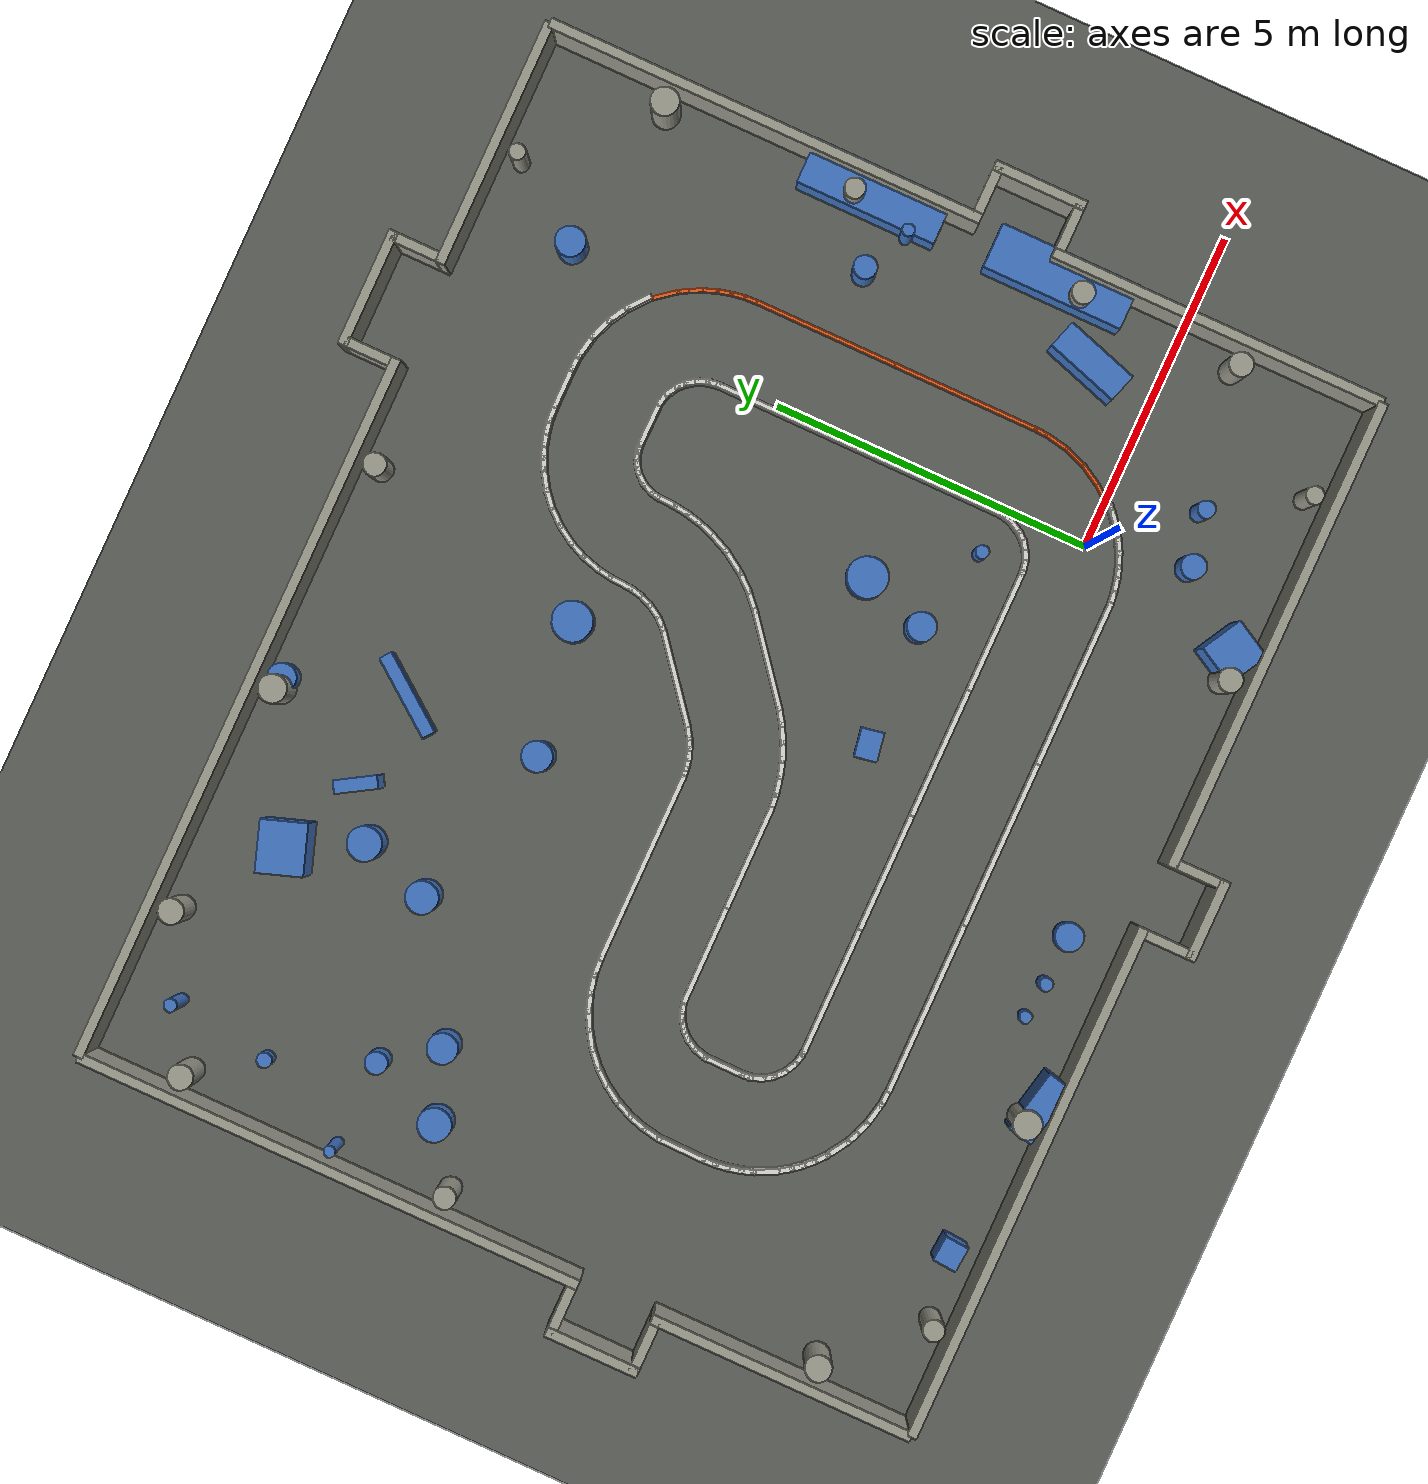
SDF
<?xml version="1.0" ?>
<sdf version="1.9">
  <!-- Generated by simulation/tools/generate_pose_dataset.py --install-gazebo-worlds from tools/pose_dataset/config/tracks.yaml (boot_lshape). Do not edit by hand: change the YAML and regenerate. -->
  <world name="default">
    <physics name="default_physics" type="dart">
      <max_step_size>0.001</max_step_size>
      <real_time_factor>1.0</real_time_factor>
      <real_time_update_rate>1000.0</real_time_update_rate>
    </physics>
    <plugin filename="gz-sim-physics-system" name="gz::sim::systems::Physics" />
    <plugin filename="gz-sim-user-commands-system" name="gz::sim::systems::UserCommands" />
    <plugin filename="gz-sim-scene-broadcaster-system" name="gz::sim::systems::SceneBroadcaster" />
    <plugin filename="gz-sim-imu-system" name="gz::sim::systems::Imu" />
    <plugin filename="gz-sim-sensors-system" name="gz::sim::systems::Sensors">
      <render_engine>ogre2</render_engine>
    </plugin>
    <light type="directional" name="sun">
      <pose>0 0 10 0 0 0</pose>
      <diffuse>0.8 0.8 0.8 1</diffuse>
      <direction>-0.5 0.5 -1</direction>
      <cast_shadows>true</cast_shadows>
    </light>
    <model name="track_curb">
      <static>true</static>
      <pose>0 0 0 0 0 0</pose>
      <link name="curb_link">
        <collision name="right0_0_0_collision">
          <pose>0.795838 0.075965 0.035000 0.000000 0.000000 0.878218</pose>
          <geometry>
            <box>
              <size>0.386390 0.060000 0.070000</size>
            </box>
          </geometry>
        </collision>
        <visual name="right0_0_0_visual">
          <pose>0.795838 0.075965 0.035000 0.000000 0.000000 0.878218</pose>
          <geometry>
            <box>
              <size>0.386390 0.060000 0.070000</size>
            </box>
          </geometry>
          <material>
            <ambient>0.9 0.35 0.1 1</ambient>
            <diffuse>0.9 0.35 0.1 1</diffuse>
          </material>
        </visual>
        <collision name="right0_1_0_collision">
          <pose>0.989773 0.355284 0.035000 0.000000 0.000000 1.042438</pose>
          <geometry>
            <box>
              <size>0.415992 0.060000 0.070000</size>
            </box>
          </geometry>
        </collision>
        <visual name="right0_1_0_visual">
          <pose>0.989773 0.355284 0.035000 0.000000 0.000000 1.042438</pose>
          <geometry>
            <box>
              <size>0.415992 0.060000 0.070000</size>
            </box>
          </geometry>
          <material>
            <ambient>0.9 0.35 0.1 1</ambient>
            <diffuse>0.9 0.35 0.1 1</diffuse>
          </material>
        </visual>
        <collision name="right0_2_0_collision">
          <pose>1.141707 0.675781 0.035000 0.000000 0.000000 1.213797</pose>
          <geometry>
            <box>
              <size>0.415992 0.060000 0.070000</size>
            </box>
          </geometry>
        </collision>
        <visual name="right0_2_0_visual">
          <pose>1.141707 0.675781 0.035000 0.000000 0.000000 1.213797</pose>
          <geometry>
            <box>
              <size>0.415992 0.060000 0.070000</size>
            </box>
          </geometry>
          <material>
            <ambient>0.9 0.35 0.1 1</ambient>
            <diffuse>0.9 0.35 0.1 1</diffuse>
          </material>
        </visual>
        <collision name="right0_3_0_collision">
          <pose>1.236763 1.017492 0.035000 0.000000 0.000000 1.385157</pose>
          <geometry>
            <box>
              <size>0.415992 0.060000 0.070000</size>
            </box>
          </geometry>
        </collision>
        <visual name="right0_3_0_visual">
          <pose>1.236763 1.017492 0.035000 0.000000 0.000000 1.385157</pose>
          <geometry>
            <box>
              <size>0.415992 0.060000 0.070000</size>
            </box>
          </geometry>
          <material>
            <ambient>0.9 0.35 0.1 1</ambient>
            <diffuse>0.9 0.35 0.1 1</diffuse>
          </material>
        </visual>
        <collision name="right0_4_0_collision">
          <pose>1.274806 1.294999 0.035000 0.000000 0.000000 1.520246</pose>
          <geometry>
            <box>
              <size>0.265400 0.060000 0.070000</size>
            </box>
          </geometry>
        </collision>
        <visual name="right0_4_0_visual">
          <pose>1.274806 1.294999 0.035000 0.000000 0.000000 1.520246</pose>
          <geometry>
            <box>
              <size>0.265400 0.060000 0.070000</size>
            </box>
          </geometry>
          <material>
            <ambient>0.9 0.35 0.1 1</ambient>
            <diffuse>0.9 0.35 0.1 1</diffuse>
          </material>
        </visual>
        <collision name="right0_5_0_collision">
          <pose>1.279996 2.523784 0.035000 0.000000 0.000000 1.570796</pose>
          <geometry>
            <box>
              <size>2.312432 0.060000 0.070000</size>
            </box>
          </geometry>
        </collision>
        <visual name="right0_5_0_visual">
          <pose>1.279996 2.523784 0.035000 0.000000 0.000000 1.570796</pose>
          <geometry>
            <box>
              <size>2.312432 0.060000 0.070000</size>
            </box>
          </geometry>
          <material>
            <ambient>0.9 0.35 0.1 1</ambient>
            <diffuse>0.9 0.35 0.1 1</diffuse>
          </material>
        </visual>
        <collision name="right0_5_1_collision">
          <pose>1.279996 4.776216 0.035000 0.000000 0.000000 1.570796</pose>
          <geometry>
            <box>
              <size>2.312432 0.060000 0.070000</size>
            </box>
          </geometry>
        </collision>
        <visual name="right0_5_1_visual">
          <pose>1.279996 4.776216 0.035000 0.000000 0.000000 1.570796</pose>
          <geometry>
            <box>
              <size>2.312432 0.060000 0.070000</size>
            </box>
          </geometry>
          <material>
            <ambient>0.9 0.35 0.1 1</ambient>
            <diffuse>0.9 0.35 0.1 1</diffuse>
          </material>
        </visual>
        <collision name="right0_6_0_collision">
          <pose>1.274806 6.005001 0.035000 0.000000 0.000000 1.621347</pose>
          <geometry>
            <box>
              <size>0.265400 0.060000 0.070000</size>
            </box>
          </geometry>
        </collision>
        <visual name="right0_6_0_visual">
          <pose>1.274806 6.005001 0.035000 0.000000 0.000000 1.621347</pose>
          <geometry>
            <box>
              <size>0.265400 0.060000 0.070000</size>
            </box>
          </geometry>
          <material>
            <ambient>0.9 0.35 0.1 1</ambient>
            <diffuse>0.9 0.35 0.1 1</diffuse>
          </material>
        </visual>
        <collision name="right0_7_0_collision">
          <pose>1.254094 6.210319 0.035000 0.000000 0.000000 1.720736</pose>
          <geometry>
            <box>
              <size>0.267830 0.060000 0.070000</size>
            </box>
          </geometry>
        </collision>
        <visual name="right0_7_0_visual">
          <pose>1.254094 6.210319 0.035000 0.000000 0.000000 1.720736</pose>
          <geometry>
            <box>
              <size>0.267830 0.060000 0.070000</size>
            </box>
          </geometry>
          <material>
            <ambient>0.9 0.35 0.1 1</ambient>
            <diffuse>0.9 0.35 0.1 1</diffuse>
          </material>
        </visual>
        <collision name="right0_8_0_collision">
          <pose>1.212873 6.413755 0.035000 0.000000 0.000000 1.820696</pose>
          <geometry>
            <box>
              <size>0.267830 0.060000 0.070000</size>
            </box>
          </geometry>
        </collision>
        <visual name="right0_8_0_visual">
          <pose>1.212873 6.413755 0.035000 0.000000 0.000000 1.820696</pose>
          <geometry>
            <box>
              <size>0.267830 0.060000 0.070000</size>
            </box>
          </geometry>
          <material>
            <ambient>0.9 0.35 0.1 1</ambient>
            <diffuse>0.9 0.35 0.1 1</diffuse>
          </material>
        </visual>
        <collision name="right0_9_0_collision">
          <pose>1.151556 6.612062 0.035000 0.000000 0.000000 1.920656</pose>
          <geometry>
            <box>
              <size>0.267830 0.060000 0.070000</size>
            </box>
          </geometry>
        </collision>
        <visual name="right0_9_0_visual">
          <pose>1.151556 6.612062 0.035000 0.000000 0.000000 1.920656</pose>
          <geometry>
            <box>
              <size>0.267830 0.060000 0.070000</size>
            </box>
          </geometry>
          <material>
            <ambient>0.9 0.35 0.1 1</ambient>
            <diffuse>0.9 0.35 0.1 1</diffuse>
          </material>
        </visual>
        <collision name="right0_10_0_collision">
          <pose>1.070755 6.803260 0.035000 0.000000 0.000000 2.020615</pose>
          <geometry>
            <box>
              <size>0.267830 0.060000 0.070000</size>
            </box>
          </geometry>
        </collision>
        <visual name="right0_10_0_visual">
          <pose>1.070755 6.803260 0.035000 0.000000 0.000000 2.020615</pose>
          <geometry>
            <box>
              <size>0.267830 0.060000 0.070000</size>
            </box>
          </geometry>
          <material>
            <ambient>0.9 0.35 0.1 1</ambient>
            <diffuse>0.9 0.35 0.1 1</diffuse>
          </material>
        </visual>
        <collision name="right0_11_0_collision">
          <pose>0.979572 6.973121 0.035000 0.000000 0.000000 2.113435</pose>
          <geometry>
            <box>
              <size>0.238159 0.060000 0.070000</size>
            </box>
          </geometry>
        </collision>
        <visual name="right0_11_0_visual">
          <pose>0.979572 6.973121 0.035000 0.000000 0.000000 2.113435</pose>
          <geometry>
            <box>
              <size>0.238159 0.060000 0.070000</size>
            </box>
          </geometry>
          <material>
            <ambient>0.9 0.35 0.1 1</ambient>
            <diffuse>0.9 0.35 0.1 1</diffuse>
          </material>
        </visual>
        <collision name="right0_12_0_collision">
          <pose>0.795085 7.224105 0.035000 0.000000 0.000000 2.241073</pose>
          <geometry>
            <box>
              <size>0.505864 0.060000 0.070000</size>
            </box>
          </geometry>
        </collision>
        <visual name="right0_12_0_visual">
          <pose>0.795085 7.224105 0.035000 0.000000 0.000000 2.241073</pose>
          <geometry>
            <box>
              <size>0.505864 0.060000 0.070000</size>
            </box>
          </geometry>
          <material>
            <ambient>0.9 0.35 0.1 1</ambient>
            <diffuse>0.9 0.35 0.1 1</diffuse>
          </material>
        </visual>
      </link>
    </model>
    <model name="track_feature">
      <static>true</static>
      <pose>0 0 0 0 0 0</pose>
      <link name="feature_link">
        <collision name="feat_box_2_collision">
          <pose>-0.581415 -2.556854 0.527100 0.000000 0.000000 -2.079561</pose>
          <geometry>
            <box>
              <size>0.652562 0.680930 1.054201</size>
            </box>
          </geometry>
        </collision>
        <visual name="feat_box_2_visual">
          <pose>-0.581415 -2.556854 0.527100 0.000000 0.000000 -2.079561</pose>
          <geometry>
            <box>
              <size>0.652562 0.680930 1.054201</size>
            </box>
          </geometry>
          <material>
            <ambient>0.25 0.45 0.75 1</ambient>
            <diffuse>0.25 0.45 0.75 1</diffuse>
          </material>
        </visual>
        <collision name="feat_box_3_collision">
          <pose>-6.160426 8.190236 0.258453 0.000000 0.000000 0.923314</pose>
          <geometry>
            <box>
              <size>1.338769 0.205793 0.516906</size>
            </box>
          </geometry>
        </collision>
        <visual name="feat_box_3_visual">
          <pose>-6.160426 8.190236 0.258453 0.000000 0.000000 0.923314</pose>
          <geometry>
            <box>
              <size>1.338769 0.205793 0.516906</size>
            </box>
          </geometry>
          <material>
            <ambient>0.25 0.45 0.75 1</ambient>
            <diffuse>0.25 0.45 0.75 1</diffuse>
          </material>
        </visual>
        <collision name="feat_box_6_collision">
          <pose>-8.921870 8.882231 0.544162 0.000000 0.000000 0.329599</pose>
          <geometry>
            <box>
              <size>0.791127 0.712381 1.088324</size>
            </box>
          </geometry>
        </collision>
        <visual name="feat_box_6_visual">
          <pose>-8.921870 8.882231 0.544162 0.000000 0.000000 0.329599</pose>
          <geometry>
            <box>
              <size>0.791127 0.712381 1.088324</size>
            </box>
          </geometry>
          <material>
            <ambient>0.25 0.45 0.75 1</ambient>
            <diffuse>0.25 0.45 0.75 1</diffuse>
          </material>
        </visual>
        <collision name="feat_box_9_collision">
          <pose>-7.639466 8.291622 0.512000 0.000000 0.000000 -1.023772</pose>
          <geometry>
            <box>
              <size>0.650131 0.202313 1.024000</size>
            </box>
          </geometry>
        </collision>
        <visual name="feat_box_9_visual">
          <pose>-7.639466 8.291622 0.512000 0.000000 0.000000 -1.023772</pose>
          <geometry>
            <box>
              <size>0.650131 0.202313 1.024000</size>
            </box>
          </geometry>
          <material>
            <ambient>0.25 0.45 0.75 1</ambient>
            <diffuse>0.25 0.45 0.75 1</diffuse>
          </material>
        </visual>
        <collision name="feat_box_17_collision">
          <pose>2.437986 1.081042 0.435741 0.000000 0.000000 -1.877875</pose>
          <geometry>
            <box>
              <size>1.191977 0.456318 0.871483</size>
            </box>
          </geometry>
        </collision>
        <visual name="feat_box_17_visual">
          <pose>2.437986 1.081042 0.435741 0.000000 0.000000 -1.877875</pose>
          <geometry>
            <box>
              <size>1.191977 0.456318 0.871483</size>
            </box>
          </geometry>
          <material>
            <ambient>0.25 0.45 0.75 1</ambient>
            <diffuse>0.25 0.45 0.75 1</diffuse>
          </material>
        </visual>
        <collision name="feat_box_22_collision">
          <pose>-7.800102 -2.750025 0.512488 0.000000 0.000000 -0.214717</pose>
          <geometry>
            <box>
              <size>0.996011 0.394849 1.024977</size>
            </box>
          </geometry>
        </collision>
        <visual name="feat_box_22_visual">
          <pose>-7.800102 -2.750025 0.512488 0.000000 0.000000 -0.214717</pose>
          <geometry>
            <box>
              <size>0.996011 0.394849 1.024977</size>
            </box>
          </geometry>
          <material>
            <ambient>0.25 0.45 0.75 1</ambient>
            <diffuse>0.25 0.45 0.75 1</diffuse>
          </material>
        </visual>
        <collision name="feat_box_30_collision">
          <pose>-10.289091 -2.465221 0.379258 0.000000 0.000000 1.489218</pose>
          <geometry>
            <box>
              <size>0.373003 0.396188 0.758515</size>
            </box>
          </geometry>
        </collision>
        <visual name="feat_box_30_visual">
          <pose>-10.289091 -2.465221 0.379258 0.000000 0.000000 1.489218</pose>
          <geometry>
            <box>
              <size>0.373003 0.396188 0.758515</size>
            </box>
          </geometry>
          <material>
            <ambient>0.25 0.45 0.75 1</ambient>
            <diffuse>0.25 0.45 0.75 1</diffuse>
          </material>
        </visual>
        <collision name="landmark_0_collision">
          <pose>-4.000000 1.700000 0.150000 0.000000 0.000000 0.174533</pose>
          <geometry>
            <box>
              <size>0.450000 0.350000 0.300000</size>
            </box>
          </geometry>
        </collision>
        <visual name="landmark_0_visual">
          <pose>-4.000000 1.700000 0.150000 0.000000 0.000000 0.174533</pose>
          <geometry>
            <box>
              <size>0.450000 0.350000 0.300000</size>
            </box>
          </geometry>
          <material>
            <ambient>0.25 0.45 0.75 1</ambient>
            <diffuse>0.25 0.45 0.75 1</diffuse>
          </material>
        </visual>
        <collision name="landmark_1_collision">
          <pose>3.400000 2.000000 0.375000 0.000000 0.000000 0.000000</pose>
          <geometry>
            <box>
              <size>0.700000 2.200000 0.750000</size>
            </box>
          </geometry>
        </collision>
        <visual name="landmark_1_visual">
          <pose>3.400000 2.000000 0.375000 0.000000 0.000000 0.000000</pose>
          <geometry>
            <box>
              <size>0.700000 2.200000 0.750000</size>
            </box>
          </geometry>
          <material>
            <ambient>0.25 0.45 0.75 1</ambient>
            <diffuse>0.25 0.45 0.75 1</diffuse>
          </material>
        </visual>
        <collision name="landmark_2_collision">
          <pose>3.400000 5.000000 0.375000 0.000000 0.000000 0.000000</pose>
          <geometry>
            <box>
              <size>0.700000 2.200000 0.750000</size>
            </box>
          </geometry>
        </collision>
        <visual name="landmark_2_visual">
          <pose>3.400000 5.000000 0.375000 0.000000 0.000000 0.000000</pose>
          <geometry>
            <box>
              <size>0.700000 2.200000 0.750000</size>
            </box>
          </geometry>
          <material>
            <ambient>0.25 0.45 0.75 1</ambient>
            <diffuse>0.25 0.45 0.75 1</diffuse>
          </material>
        </visual>
        <collision name="feat_cyl_1_collision">
          <pose>-1.774489 2.749740 0.251477 0.000000 0.000000 0.000000</pose>
          <geometry>
            <cylinder>
              <radius>0.314614</radius>
              <length>0.502954</length>
            </cylinder>
          </geometry>
        </collision>
        <visual name="feat_cyl_1_visual">
          <pose>-1.774489 2.749740 0.251477 0.000000 0.000000 0.000000</pose>
          <geometry>
            <cylinder>
              <radius>0.314614</radius>
              <length>0.502954</length>
            </cylinder>
          </geometry>
          <material>
            <ambient>0.25 0.45 0.75 1</ambient>
            <diffuse>0.25 0.45 0.75 1</diffuse>
          </material>
        </visual>
        <collision name="feat_cyl_4_collision">
          <pose>-6.694799 -2.059456 0.194213 0.000000 0.000000 0.000000</pose>
          <geometry>
            <cylinder>
              <radius>0.096125</radius>
              <length>0.388426</length>
            </cylinder>
          </geometry>
        </collision>
        <visual name="feat_cyl_4_visual">
          <pose>-6.694799 -2.059456 0.194213 0.000000 0.000000 0.000000</pose>
          <geometry>
            <cylinder>
              <radius>0.096125</radius>
              <length>0.388426</length>
            </cylinder>
          </geometry>
          <material>
            <ambient>0.25 0.45 0.75 1</ambient>
            <diffuse>0.25 0.45 0.75 1</diffuse>
          </material>
        </visual>
        <collision name="feat_cyl_5_collision">
          <pose>-11.248425 6.349912 0.329447 0.000000 0.000000 0.000000</pose>
          <geometry>
            <cylinder>
              <radius>0.171465</radius>
              <length>0.658894</length>
            </cylinder>
          </geometry>
        </collision>
        <visual name="feat_cyl_5_visual">
          <pose>-11.248425 6.349912 0.329447 0.000000 0.000000 0.000000</pose>
          <geometry>
            <cylinder>
              <radius>0.171465</radius>
              <length>0.658894</length>
            </cylinder>
          </geometry>
          <material>
            <ambient>0.25 0.45 0.75 1</ambient>
            <diffuse>0.25 0.45 0.75 1</diffuse>
          </material>
        </visual>
        <collision name="feat_cyl_7_collision">
          <pose>-2.129406 1.742207 0.508666 0.000000 0.000000 0.000000</pose>
          <geometry>
            <cylinder>
              <radius>0.223696</radius>
              <length>1.017332</length>
            </cylinder>
          </geometry>
        </collision>
        <visual name="feat_cyl_7_visual">
          <pose>-2.129406 1.742207 0.508666 0.000000 0.000000 0.000000</pose>
          <geometry>
            <cylinder>
              <radius>0.223696</radius>
              <length>1.017332</length>
            </cylinder>
          </geometry>
          <material>
            <ambient>0.25 0.45 0.75 1</ambient>
            <diffuse>0.25 0.45 0.75 1</diffuse>
          </material>
        </visual>
        <collision name="feat_cyl_8_collision">
          <pose>-11.724675 5.199260 0.315476 0.000000 0.000000 0.000000</pose>
          <geometry>
            <cylinder>
              <radius>0.257579</radius>
              <length>0.630951</length>
            </cylinder>
          </geometry>
        </collision>
        <visual name="feat_cyl_8_visual">
          <pose>-11.724675 5.199260 0.315476 0.000000 0.000000 0.000000</pose>
          <geometry>
            <cylinder>
              <radius>0.257579</radius>
              <length>0.630951</length>
            </cylinder>
          </geometry>
          <material>
            <ambient>0.25 0.45 0.75 1</ambient>
            <diffuse>0.25 0.45 0.75 1</diffuse>
          </material>
        </visual>
        <collision name="feat_cyl_10_collision">
          <pose>-8.383253 7.828350 0.425368 0.000000 0.000000 0.000000</pose>
          <geometry>
            <cylinder>
              <radius>0.262843</radius>
              <length>0.850736</length>
            </cylinder>
          </geometry>
        </collision>
        <visual name="feat_cyl_10_visual">
          <pose>-8.383253 7.828350 0.425368 0.000000 0.000000 0.000000</pose>
          <geometry>
            <cylinder>
              <radius>0.262843</radius>
              <length>0.850736</length>
            </cylinder>
          </geometry>
          <material>
            <ambient>0.25 0.45 0.75 1</ambient>
            <diffuse>0.25 0.45 0.75 1</diffuse>
          </material>
        </visual>
        <collision name="feat_cyl_11_collision">
          <pose>-6.684945 9.968727 0.267723 0.000000 0.000000 0.000000</pose>
          <geometry>
            <cylinder>
              <radius>0.219137</radius>
              <length>0.535447</length>
            </cylinder>
          </geometry>
        </collision>
        <visual name="feat_cyl_11_visual">
          <pose>-6.684945 9.968727 0.267723 0.000000 0.000000 0.000000</pose>
          <geometry>
            <cylinder>
              <radius>0.219137</radius>
              <length>0.535447</length>
            </cylinder>
          </geometry>
          <material>
            <ambient>0.25 0.45 0.75 1</ambient>
            <diffuse>0.25 0.45 0.75 1</diffuse>
          </material>
        </visual>
        <collision name="feat_cyl_12_collision">
          <pose>-11.666292 9.393082 0.574413 0.000000 0.000000 0.000000</pose>
          <geometry>
            <cylinder>
              <radius>0.099789</radius>
              <length>1.148826</length>
            </cylinder>
          </geometry>
        </collision>
        <visual name="feat_cyl_12_visual">
          <pose>-11.666292 9.393082 0.574413 0.000000 0.000000 0.000000</pose>
          <geometry>
            <cylinder>
              <radius>0.099789</radius>
              <length>1.148826</length>
            </cylinder>
          </geometry>
          <material>
            <ambient>0.25 0.45 0.75 1</ambient>
            <diffuse>0.25 0.45 0.75 1</diffuse>
          </material>
        </visual>
        <collision name="feat_cyl_13_collision">
          <pose>3.052305 4.317826 0.491781 0.000000 0.000000 0.000000</pose>
          <geometry>
            <cylinder>
              <radius>0.095647</radius>
              <length>0.983562</length>
            </cylinder>
          </geometry>
        </collision>
        <visual name="feat_cyl_13_visual">
          <pose>3.052305 4.317826 0.491781 0.000000 0.000000 0.000000</pose>
          <geometry>
            <cylinder>
              <radius>0.095647</radius>
              <length>0.983562</length>
            </cylinder>
          </geometry>
          <material>
            <ambient>0.25 0.45 0.75 1</ambient>
            <diffuse>0.25 0.45 0.75 1</diffuse>
          </material>
        </visual>
        <collision name="feat_cyl_14_collision">
          <pose>0.869227 8.741721 0.430245 0.000000 0.000000 0.000000</pose>
          <geometry>
            <cylinder>
              <radius>0.230710</radius>
              <length>0.860490</length>
            </cylinder>
          </geometry>
        </collision>
        <visual name="feat_cyl_14_visual">
          <pose>0.869227 8.741721 0.430245 0.000000 0.000000 0.000000</pose>
          <geometry>
            <cylinder>
              <radius>0.230710</radius>
              <length>0.860490</length>
            </cylinder>
          </geometry>
          <material>
            <ambient>0.25 0.45 0.75 1</ambient>
            <diffuse>0.25 0.45 0.75 1</diffuse>
          </material>
        </visual>
        <collision name="feat_cyl_15_collision">
          <pose>-5.357916 -2.153753 0.207390 0.000000 0.000000 0.000000</pose>
          <geometry>
            <cylinder>
              <radius>0.218447</radius>
              <length>0.414781</length>
            </cylinder>
          </geometry>
        </collision>
        <visual name="feat_cyl_15_visual">
          <pose>-5.357916 -2.153753 0.207390 0.000000 0.000000 0.000000</pose>
          <geometry>
            <cylinder>
              <radius>0.218447</radius>
              <length>0.414781</length>
            </cylinder>
          </geometry>
          <material>
            <ambient>0.25 0.45 0.75 1</ambient>
            <diffuse>0.25 0.45 0.75 1</diffuse>
          </material>
        </visual>
        <collision name="feat_cyl_16_collision">
          <pose>-4.165591 6.422975 0.336970 0.000000 0.000000 0.000000</pose>
          <geometry>
            <cylinder>
              <radius>0.309782</radius>
              <length>0.673940</length>
            </cylinder>
          </geometry>
        </collision>
        <visual name="feat_cyl_16_visual">
          <pose>-4.165591 6.422975 0.336970 0.000000 0.000000 0.000000</pose>
          <geometry>
            <cylinder>
              <radius>0.309782</radius>
              <length>0.673940</length>
            </cylinder>
          </geometry>
          <material>
            <ambient>0.25 0.45 0.75 1</ambient>
            <diffuse>0.25 0.45 0.75 1</diffuse>
          </material>
        </visual>
        <collision name="feat_cyl_18_collision">
          <pose>1.152145 -1.325701 0.479255 0.000000 0.000000 0.000000</pose>
          <geometry>
            <cylinder>
              <radius>0.135182</radius>
              <length>0.958511</length>
            </cylinder>
          </geometry>
        </collision>
        <visual name="feat_cyl_18_visual">
          <pose>1.152145 -1.325701 0.479255 0.000000 0.000000 0.000000</pose>
          <geometry>
            <cylinder>
              <radius>0.135182</radius>
              <length>0.958511</length>
            </cylinder>
          </geometry>
          <material>
            <ambient>0.25 0.45 0.75 1</ambient>
            <diffuse>0.25 0.45 0.75 1</diffuse>
          </material>
        </visual>
        <collision name="feat_cyl_19_collision">
          <pose>3.578357 5.291748 0.212490 0.000000 0.000000 0.000000</pose>
          <geometry>
            <cylinder>
              <radius>0.204324</radius>
              <length>0.424980</length>
            </cylinder>
          </geometry>
        </collision>
        <visual name="feat_cyl_19_visual">
          <pose>3.578357 5.291748 0.212490 0.000000 0.000000 0.000000</pose>
          <geometry>
            <cylinder>
              <radius>0.204324</radius>
              <length>0.424980</length>
            </cylinder>
          </geometry>
          <material>
            <ambient>0.25 0.45 0.75 1</ambient>
            <diffuse>0.25 0.45 0.75 1</diffuse>
          </material>
        </visual>
        <collision name="feat_cyl_20_collision">
          <pose>0.331226 -1.519883 0.392856 0.000000 0.000000 0.000000</pose>
          <geometry>
            <cylinder>
              <radius>0.191734</radius>
              <length>0.785712</length>
            </cylinder>
          </geometry>
        </collision>
        <visual name="feat_cyl_20_visual">
          <pose>0.331226 -1.519883 0.392856 0.000000 0.000000 0.000000</pose>
          <geometry>
            <cylinder>
              <radius>0.191734</radius>
              <length>0.785712</length>
            </cylinder>
          </geometry>
          <material>
            <ambient>0.25 0.45 0.75 1</ambient>
            <diffuse>0.25 0.45 0.75 1</diffuse>
          </material>
        </visual>
        <collision name="feat_cyl_21_collision">
          <pose>-0.755450 1.382525 0.382097 0.000000 0.000000 0.000000</pose>
          <geometry>
            <cylinder>
              <radius>0.103910</radius>
              <length>0.764194</length>
            </cylinder>
          </geometry>
        </collision>
        <visual name="feat_cyl_21_visual">
          <pose>-0.755450 1.382525 0.382097 0.000000 0.000000 0.000000</pose>
          <geometry>
            <cylinder>
              <radius>0.103910</radius>
              <length>0.764194</length>
            </cylinder>
          </geometry>
          <material>
            <ambient>0.25 0.45 0.75 1</ambient>
            <diffuse>0.25 0.45 0.75 1</diffuse>
          </material>
        </visual>
        <collision name="feat_cyl_23_collision">
          <pose>-8.753124 6.739991 0.413110 0.000000 0.000000 0.000000</pose>
          <geometry>
            <cylinder>
              <radius>0.248951</radius>
              <length>0.826221</length>
            </cylinder>
          </geometry>
        </collision>
        <visual name="feat_cyl_23_visual">
          <pose>-8.753124 6.739991 0.413110 0.000000 0.000000 0.000000</pose>
          <geometry>
            <cylinder>
              <radius>0.248951</radius>
              <length>0.826221</length>
            </cylinder>
          </geometry>
          <material>
            <ambient>0.25 0.45 0.75 1</ambient>
            <diffuse>0.25 0.45 0.75 1</diffuse>
          </material>
        </visual>
        <collision name="feat_cyl_24_collision">
          <pose>-6.127524 -2.114447 0.298246 0.000000 0.000000 0.000000</pose>
          <geometry>
            <cylinder>
              <radius>0.102054</radius>
              <length>0.596491</length>
            </cylinder>
          </geometry>
        </collision>
        <visual name="feat_cyl_24_visual">
          <pose>-6.127524 -2.114447 0.298246 0.000000 0.000000 0.000000</pose>
          <geometry>
            <cylinder>
              <radius>0.102054</radius>
              <length>0.596491</length>
            </cylinder>
          </geometry>
          <material>
            <ambient>0.25 0.45 0.75 1</ambient>
            <diffuse>0.25 0.45 0.75 1</diffuse>
          </material>
        </visual>
        <collision name="feat_cyl_25_collision">
          <pose>-6.173185 6.054653 0.525848 0.000000 0.000000 0.000000</pose>
          <geometry>
            <cylinder>
              <radius>0.232763</radius>
              <length>1.051696</length>
            </cylinder>
          </geometry>
        </collision>
        <visual name="feat_cyl_25_visual">
          <pose>-6.173185 6.054653 0.525848 0.000000 0.000000 0.000000</pose>
          <geometry>
            <cylinder>
              <radius>0.232763</radius>
              <length>1.051696</length>
            </cylinder>
          </geometry>
          <material>
            <ambient>0.25 0.45 0.75 1</ambient>
            <diffuse>0.25 0.45 0.75 1</diffuse>
          </material>
        </visual>
        <collision name="feat_cyl_26_collision">
          <pose>-12.632936 6.407135 0.598371 0.000000 0.000000 0.000000</pose>
          <geometry>
            <cylinder>
              <radius>0.087629</radius>
              <length>1.196742</length>
            </cylinder>
          </geometry>
        </collision>
        <visual name="feat_cyl_26_visual">
          <pose>-12.632936 6.407135 0.598371 0.000000 0.000000 0.000000</pose>
          <geometry>
            <cylinder>
              <radius>0.087629</radius>
              <length>1.196742</length>
            </cylinder>
          </geometry>
          <material>
            <ambient>0.25 0.45 0.75 1</ambient>
            <diffuse>0.25 0.45 0.75 1</diffuse>
          </material>
        </visual>
        <collision name="feat_cyl_27_collision">
          <pose>2.310290 4.667056 0.440040 0.000000 0.000000 0.000000</pose>
          <geometry>
            <cylinder>
              <radius>0.178377</radius>
              <length>0.880081</length>
            </cylinder>
          </geometry>
        </collision>
        <visual name="feat_cyl_27_visual">
          <pose>2.310290 4.667056 0.440040 0.000000 0.000000 0.000000</pose>
          <geometry>
            <cylinder>
              <radius>0.178377</radius>
              <length>0.880081</length>
            </cylinder>
          </geometry>
          <material>
            <ambient>0.25 0.45 0.75 1</ambient>
            <diffuse>0.25 0.45 0.75 1</diffuse>
          </material>
        </visual>
        <collision name="feat_cyl_28_collision">
          <pose>-11.924055 7.880588 0.205456 0.000000 0.000000 0.000000</pose>
          <geometry>
            <cylinder>
              <radius>0.117067</radius>
              <length>0.410912</length>
            </cylinder>
          </geometry>
        </collision>
        <visual name="feat_cyl_28_visual">
          <pose>-11.924055 7.880588 0.205456 0.000000 0.000000 0.000000</pose>
          <geometry>
            <cylinder>
              <radius>0.117067</radius>
              <length>0.410912</length>
            </cylinder>
          </geometry>
          <material>
            <ambient>0.25 0.45 0.75 1</ambient>
            <diffuse>0.25 0.45 0.75 1</diffuse>
          </material>
        </visual>
        <collision name="feat_cyl_29_collision">
          <pose>-10.640033 5.551522 0.393729 0.000000 0.000000 0.000000</pose>
          <geometry>
            <cylinder>
              <radius>0.234279</radius>
              <length>0.787458</length>
            </cylinder>
          </geometry>
        </collision>
        <visual name="feat_cyl_29_visual">
          <pose>-10.640033 5.551522 0.393729 0.000000 0.000000 0.000000</pose>
          <geometry>
            <cylinder>
              <radius>0.234279</radius>
              <length>0.787458</length>
            </cylinder>
          </geometry>
          <material>
            <ambient>0.25 0.45 0.75 1</ambient>
            <diffuse>0.25 0.45 0.75 1</diffuse>
          </material>
        </visual>
      </link>
    </model>
    <model name="track_ground">
      <static>true</static>
      <pose>0 0 0 0 0 0</pose>
      <link name="ground_link">
        <collision name="ground_collision">
          <pose>-3.866297 2.778926 -0.025000 0.000000 0.000000 0.000000</pose>
          <geometry>
            <box>
              <size>80.000000 80.000000 0.050000</size>
            </box>
          </geometry>
          <surface>
            <friction>
              <ode>
                <mu>1.2</mu>
                <mu2>1.2</mu2>
              </ode>
            </friction>
            <contact>
              <ode>
                <kp>100000.0</kp>
                <kd>10.0</kd>
              </ode>
            </contact>
          </surface>
        </collision>
        <visual name="ground_visual">
          <pose>-3.866297 2.778926 -0.025000 0.000000 0.000000 0.000000</pose>
          <geometry>
            <box>
              <size>80.000000 80.000000 0.050000</size>
            </box>
          </geometry>
          <material>
            <ambient>0.35 0.36 0.34 1</ambient>
            <diffuse>0.35 0.36 0.34 1</diffuse>
          </material>
        </visual>
      </link>
    </model>
    <model name="track_room">
      <static>true</static>
      <pose>0 0 0 0 0 0</pose>
      <link name="room_link">
        <collision name="hall_0_0_collision">
          <pose>-8.838522 -3.000000 0.600000 0.000000 0.000000 0.000000</pose>
          <geometry>
            <box>
              <size>8.122956 0.150000 1.200000</size>
            </box>
          </geometry>
        </collision>
        <visual name="hall_0_0_visual">
          <pose>-8.838522 -3.000000 0.600000 0.000000 0.000000 0.000000</pose>
          <geometry>
            <box>
              <size>8.122956 0.150000 1.200000</size>
            </box>
          </geometry>
          <material>
            <ambient>0.6 0.6 0.55 1</ambient>
            <diffuse>0.6 0.6 0.55 1</diffuse>
          </material>
        </visual>
        <collision name="hall_0_90_collision">
          <pose>-0.104746 -3.000000 0.600000 0.000000 0.000000 0.000000</pose>
          <geometry>
            <box>
              <size>7.409492 0.150000 1.200000</size>
            </box>
          </geometry>
        </collision>
        <visual name="hall_0_90_visual">
          <pose>-0.104746 -3.000000 0.600000 0.000000 0.000000 0.000000</pose>
          <geometry>
            <box>
              <size>7.409492 0.150000 1.200000</size>
            </box>
          </geometry>
          <material>
            <ambient>0.6 0.6 0.55 1</ambient>
            <diffuse>0.6 0.6 0.55 1</diffuse>
          </material>
        </visual>
        <collision name="hall_niche_0_collision">
          <pose>-4.293268 -3.800000 0.600000 0.000000 0.000000 0.000000</pose>
          <geometry>
            <box>
              <size>1.267552 0.150000 1.200000</size>
            </box>
          </geometry>
        </collision>
        <visual name="hall_niche_0_visual">
          <pose>-4.293268 -3.800000 0.600000 0.000000 0.000000 0.000000</pose>
          <geometry>
            <box>
              <size>1.267552 0.150000 1.200000</size>
            </box>
          </geometry>
          <material>
            <ambient>0.6 0.6 0.55 1</ambient>
            <diffuse>0.6 0.6 0.55 1</diffuse>
          </material>
        </visual>
        <collision name="hall_jamb_0_-1_collision">
          <pose>-4.852044 -3.400000 0.600000 0.000000 0.000000 0.000000</pose>
          <geometry>
            <box>
              <size>0.150000 0.800000 1.200000</size>
            </box>
          </geometry>
        </collision>
        <visual name="hall_jamb_0_-1_visual">
          <pose>-4.852044 -3.400000 0.600000 0.000000 0.000000 0.000000</pose>
          <geometry>
            <box>
              <size>0.150000 0.800000 1.200000</size>
            </box>
          </geometry>
          <material>
            <ambient>0.6 0.6 0.55 1</ambient>
            <diffuse>0.6 0.6 0.55 1</diffuse>
          </material>
        </visual>
        <collision name="hall_jamb_0_1_collision">
          <pose>-3.734492 -3.400000 0.600000 0.000000 0.000000 0.000000</pose>
          <geometry>
            <box>
              <size>0.150000 0.800000 1.200000</size>
            </box>
          </geometry>
        </collision>
        <visual name="hall_jamb_0_1_visual">
          <pose>-3.734492 -3.400000 0.600000 0.000000 0.000000 0.000000</pose>
          <geometry>
            <box>
              <size>0.150000 0.800000 1.200000</size>
            </box>
          </geometry>
          <material>
            <ambient>0.6 0.6 0.55 1</ambient>
            <diffuse>0.6 0.6 0.55 1</diffuse>
          </material>
        </visual>
        <collision name="hall_1_0_collision">
          <pose>3.600000 -0.368566 0.600000 0.000000 0.000000 1.570796</pose>
          <geometry>
            <box>
              <size>5.262867 0.150000 1.200000</size>
            </box>
          </geometry>
        </collision>
        <visual name="hall_1_0_visual">
          <pose>3.600000 -0.368566 0.600000 0.000000 0.000000 1.570796</pose>
          <geometry>
            <box>
              <size>5.262867 0.150000 1.200000</size>
            </box>
          </geometry>
          <material>
            <ambient>0.6 0.6 0.55 1</ambient>
            <diffuse>0.6 0.6 0.55 1</diffuse>
          </material>
        </visual>
        <collision name="hall_1_64_collision">
          <pose>3.600000 6.861199 0.600000 0.000000 0.000000 1.570796</pose>
          <geometry>
            <box>
              <size>6.877601 0.150000 1.200000</size>
            </box>
          </geometry>
        </collision>
        <visual name="hall_1_64_visual">
          <pose>3.600000 6.861199 0.600000 0.000000 0.000000 1.570796</pose>
          <geometry>
            <box>
              <size>6.877601 0.150000 1.200000</size>
            </box>
          </geometry>
          <material>
            <ambient>0.6 0.6 0.55 1</ambient>
            <diffuse>0.6 0.6 0.55 1</diffuse>
          </material>
        </visual>
        <collision name="hall_niche_1_collision">
          <pose>4.400000 2.842633 0.600000 0.000000 0.000000 1.570796</pose>
          <geometry>
            <box>
              <size>1.459531 0.150000 1.200000</size>
            </box>
          </geometry>
        </collision>
        <visual name="hall_niche_1_visual">
          <pose>4.400000 2.842633 0.600000 0.000000 0.000000 1.570796</pose>
          <geometry>
            <box>
              <size>1.459531 0.150000 1.200000</size>
            </box>
          </geometry>
          <material>
            <ambient>0.6 0.6 0.55 1</ambient>
            <diffuse>0.6 0.6 0.55 1</diffuse>
          </material>
        </visual>
        <collision name="hall_jamb_1_-1_collision">
          <pose>4.000000 2.187867 0.600000 0.000000 0.000000 1.570796</pose>
          <geometry>
            <box>
              <size>0.150000 0.800000 1.200000</size>
            </box>
          </geometry>
        </collision>
        <visual name="hall_jamb_1_-1_visual">
          <pose>4.000000 2.187867 0.600000 0.000000 0.000000 1.570796</pose>
          <geometry>
            <box>
              <size>0.150000 0.800000 1.200000</size>
            </box>
          </geometry>
          <material>
            <ambient>0.6 0.6 0.55 1</ambient>
            <diffuse>0.6 0.6 0.55 1</diffuse>
          </material>
        </visual>
        <collision name="hall_jamb_1_1_collision">
          <pose>4.000000 3.497399 0.600000 0.000000 0.000000 1.570796</pose>
          <geometry>
            <box>
              <size>0.150000 0.800000 1.200000</size>
            </box>
          </geometry>
        </collision>
        <visual name="hall_jamb_1_1_visual">
          <pose>4.000000 3.497399 0.600000 0.000000 0.000000 1.570796</pose>
          <geometry>
            <box>
              <size>0.150000 0.800000 1.200000</size>
            </box>
          </geometry>
          <material>
            <ambient>0.6 0.6 0.55 1</ambient>
            <diffuse>0.6 0.6 0.55 1</diffuse>
          </material>
        </visual>
        <collision name="hall_2_0_collision">
          <pose>1.679348 10.300000 0.600000 0.000000 0.000000 3.141593</pose>
          <geometry>
            <box>
              <size>3.841303 0.150000 1.200000</size>
            </box>
          </geometry>
        </collision>
        <visual name="hall_2_0_visual">
          <pose>1.679348 10.300000 0.600000 0.000000 0.000000 3.141593</pose>
          <geometry>
            <box>
              <size>3.841303 0.150000 1.200000</size>
            </box>
          </geometry>
          <material>
            <ambient>0.6 0.6 0.55 1</ambient>
            <diffuse>0.6 0.6 0.55 1</diffuse>
          </material>
        </visual>
        <collision name="hall_2_53_collision">
          <pose>-7.329607 10.300000 0.600000 0.000000 0.000000 3.141593</pose>
          <geometry>
            <box>
              <size>11.140787 0.150000 1.200000</size>
            </box>
          </geometry>
        </collision>
        <visual name="hall_2_53_visual">
          <pose>-7.329607 10.300000 0.600000 0.000000 0.000000 3.141593</pose>
          <geometry>
            <box>
              <size>11.140787 0.150000 1.200000</size>
            </box>
          </geometry>
          <material>
            <ambient>0.6 0.6 0.55 1</ambient>
            <diffuse>0.6 0.6 0.55 1</diffuse>
          </material>
        </visual>
        <collision name="hall_niche_2_collision">
          <pose>-1.000258 11.100000 0.600000 0.000000 0.000000 3.141593</pose>
          <geometry>
            <box>
              <size>1.817910 0.150000 1.200000</size>
            </box>
          </geometry>
        </collision>
        <visual name="hall_niche_2_visual">
          <pose>-1.000258 11.100000 0.600000 0.000000 0.000000 3.141593</pose>
          <geometry>
            <box>
              <size>1.817910 0.150000 1.200000</size>
            </box>
          </geometry>
          <material>
            <ambient>0.6 0.6 0.55 1</ambient>
            <diffuse>0.6 0.6 0.55 1</diffuse>
          </material>
        </visual>
        <collision name="hall_jamb_2_-1_collision">
          <pose>-0.166303 10.700000 0.600000 0.000000 0.000000 3.141593</pose>
          <geometry>
            <box>
              <size>0.150000 0.800000 1.200000</size>
            </box>
          </geometry>
        </collision>
        <visual name="hall_jamb_2_-1_visual">
          <pose>-0.166303 10.700000 0.600000 0.000000 0.000000 3.141593</pose>
          <geometry>
            <box>
              <size>0.150000 0.800000 1.200000</size>
            </box>
          </geometry>
          <material>
            <ambient>0.6 0.6 0.55 1</ambient>
            <diffuse>0.6 0.6 0.55 1</diffuse>
          </material>
        </visual>
        <collision name="hall_jamb_2_1_collision">
          <pose>-1.834213 10.700000 0.600000 0.000000 0.000000 3.141593</pose>
          <geometry>
            <box>
              <size>0.150000 0.800000 1.200000</size>
            </box>
          </geometry>
        </collision>
        <visual name="hall_jamb_2_1_visual">
          <pose>-1.834213 10.700000 0.600000 0.000000 0.000000 3.141593</pose>
          <geometry>
            <box>
              <size>0.150000 0.800000 1.200000</size>
            </box>
          </geometry>
          <material>
            <ambient>0.6 0.6 0.55 1</ambient>
            <diffuse>0.6 0.6 0.55 1</diffuse>
          </material>
        </visual>
        <collision name="hall_3_0_collision">
          <pose>-12.900000 6.307811 0.600000 0.000000 0.000000 -1.570796</pose>
          <geometry>
            <box>
              <size>7.984378 0.150000 1.200000</size>
            </box>
          </geometry>
        </collision>
        <visual name="hall_3_0_visual">
          <pose>-12.900000 6.307811 0.600000 0.000000 0.000000 -1.570796</pose>
          <geometry>
            <box>
              <size>7.984378 0.150000 1.200000</size>
            </box>
          </geometry>
          <material>
            <ambient>0.6 0.6 0.55 1</ambient>
            <diffuse>0.6 0.6 0.55 1</diffuse>
          </material>
        </visual>
        <collision name="hall_3_91_collision">
          <pose>-12.900000 -0.927635 0.600000 0.000000 0.000000 -1.570796</pose>
          <geometry>
            <box>
              <size>4.144729 0.150000 1.200000</size>
            </box>
          </geometry>
        </collision>
        <visual name="hall_3_91_visual">
          <pose>-12.900000 -0.927635 0.600000 0.000000 0.000000 -1.570796</pose>
          <geometry>
            <box>
              <size>4.144729 0.150000 1.200000</size>
            </box>
          </geometry>
          <material>
            <ambient>0.6 0.6 0.55 1</ambient>
            <diffuse>0.6 0.6 0.55 1</diffuse>
          </material>
        </visual>
        <collision name="hall_niche_3_collision">
          <pose>-13.700000 1.730175 0.600000 0.000000 0.000000 -1.570796</pose>
          <geometry>
            <box>
              <size>1.470892 0.150000 1.200000</size>
            </box>
          </geometry>
        </collision>
        <visual name="hall_niche_3_visual">
          <pose>-13.700000 1.730175 0.600000 0.000000 0.000000 -1.570796</pose>
          <geometry>
            <box>
              <size>1.470892 0.150000 1.200000</size>
            </box>
          </geometry>
          <material>
            <ambient>0.6 0.6 0.55 1</ambient>
            <diffuse>0.6 0.6 0.55 1</diffuse>
          </material>
        </visual>
        <collision name="hall_jamb_3_-1_collision">
          <pose>-13.300000 2.390622 0.600000 0.000000 0.000000 -1.570796</pose>
          <geometry>
            <box>
              <size>0.150000 0.800000 1.200000</size>
            </box>
          </geometry>
        </collision>
        <visual name="hall_jamb_3_-1_visual">
          <pose>-13.300000 2.390622 0.600000 0.000000 0.000000 -1.570796</pose>
          <geometry>
            <box>
              <size>0.150000 0.800000 1.200000</size>
            </box>
          </geometry>
          <material>
            <ambient>0.6 0.6 0.55 1</ambient>
            <diffuse>0.6 0.6 0.55 1</diffuse>
          </material>
        </visual>
        <collision name="hall_jamb_3_1_collision">
          <pose>-13.300000 1.069729 0.600000 0.000000 0.000000 -1.570796</pose>
          <geometry>
            <box>
              <size>0.150000 0.800000 1.200000</size>
            </box>
          </geometry>
        </collision>
        <visual name="hall_jamb_3_1_visual">
          <pose>-13.300000 1.069729 0.600000 0.000000 0.000000 -1.570796</pose>
          <geometry>
            <box>
              <size>0.150000 0.800000 1.200000</size>
            </box>
          </geometry>
          <material>
            <ambient>0.6 0.6 0.55 1</ambient>
            <diffuse>0.6 0.6 0.55 1</diffuse>
          </material>
        </visual>
        <collision name="column_0_15_collision">
          <pose>-11.355991 -2.650000 0.600000 0.000000 0.000000 0.000000</pose>
          <geometry>
            <cylinder>
              <radius>0.164377</radius>
              <length>1.200000</length>
            </cylinder>
          </geometry>
        </collision>
        <visual name="column_0_15_visual">
          <pose>-11.355991 -2.650000 0.600000 0.000000 0.000000 0.000000</pose>
          <geometry>
            <cylinder>
              <radius>0.164377</radius>
              <length>1.200000</length>
            </cylinder>
          </geometry>
          <material>
            <ambient>0.6 0.6 0.55 1</ambient>
            <diffuse>0.6 0.6 0.55 1</diffuse>
          </material>
        </visual>
        <collision name="column_0_48_collision">
          <pose>-8.079122 -2.650000 0.600000 0.000000 0.000000 0.000000</pose>
          <geometry>
            <cylinder>
              <radius>0.217591</radius>
              <length>1.200000</length>
            </cylinder>
          </geometry>
        </collision>
        <visual name="column_0_48_visual">
          <pose>-8.079122 -2.650000 0.600000 0.000000 0.000000 0.000000</pose>
          <geometry>
            <cylinder>
              <radius>0.217591</radius>
              <length>1.200000</length>
            </cylinder>
          </geometry>
          <material>
            <ambient>0.6 0.6 0.55 1</ambient>
            <diffuse>0.6 0.6 0.55 1</diffuse>
          </material>
        </visual>
        <collision name="column_0_119_collision">
          <pose>-0.982741 -2.650000 0.600000 0.000000 0.000000 0.000000</pose>
          <geometry>
            <cylinder>
              <radius>0.185457</radius>
              <length>1.200000</length>
            </cylinder>
          </geometry>
        </collision>
        <visual name="column_0_119_visual">
          <pose>-0.982741 -2.650000 0.600000 0.000000 0.000000 0.000000</pose>
          <geometry>
            <cylinder>
              <radius>0.185457</radius>
              <length>1.200000</length>
            </cylinder>
          </geometry>
          <material>
            <ambient>0.6 0.6 0.55 1</ambient>
            <diffuse>0.6 0.6 0.55 1</diffuse>
          </material>
        </visual>
        <collision name="column_0_148_collision">
          <pose>1.965624 -2.650000 0.600000 0.000000 0.000000 0.000000</pose>
          <geometry>
            <cylinder>
              <radius>0.136687</radius>
              <length>1.200000</length>
            </cylinder>
          </geometry>
        </collision>
        <visual name="column_0_148_visual">
          <pose>1.965624 -2.650000 0.600000 0.000000 0.000000 0.000000</pose>
          <geometry>
            <cylinder>
              <radius>0.136687</radius>
              <length>1.200000</length>
            </cylinder>
          </geometry>
          <material>
            <ambient>0.6 0.6 0.55 1</ambient>
            <diffuse>0.6 0.6 0.55 1</diffuse>
          </material>
        </visual>
        <collision name="column_1_21_collision">
          <pose>3.250000 -0.889792 0.600000 0.000000 0.000000 0.000000</pose>
          <geometry>
            <cylinder>
              <radius>0.182546</radius>
              <length>1.200000</length>
            </cylinder>
          </geometry>
        </collision>
        <visual name="column_1_21_visual">
          <pose>3.250000 -0.889792 0.600000 0.000000 0.000000 0.000000</pose>
          <geometry>
            <cylinder>
              <radius>0.182546</radius>
              <length>1.200000</length>
            </cylinder>
          </geometry>
          <material>
            <ambient>0.6 0.6 0.55 1</ambient>
            <diffuse>0.6 0.6 0.55 1</diffuse>
          </material>
        </visual>
        <collision name="column_1_46_collision">
          <pose>3.250000 1.628248 0.600000 0.000000 0.000000 0.000000</pose>
          <geometry>
            <cylinder>
              <radius>0.174364</radius>
              <length>1.200000</length>
            </cylinder>
          </geometry>
        </collision>
        <visual name="column_1_46_visual">
          <pose>3.250000 1.628248 0.600000 0.000000 0.000000 0.000000</pose>
          <geometry>
            <cylinder>
              <radius>0.174364</radius>
              <length>1.200000</length>
            </cylinder>
          </geometry>
          <material>
            <ambient>0.6 0.6 0.55 1</ambient>
            <diffuse>0.6 0.6 0.55 1</diffuse>
          </material>
        </visual>
        <collision name="column_1_82_collision">
          <pose>3.250000 5.271839 0.600000 0.000000 0.000000 0.000000</pose>
          <geometry>
            <cylinder>
              <radius>0.157553</radius>
              <length>1.200000</length>
            </cylinder>
          </geometry>
        </collision>
        <visual name="column_1_82_visual">
          <pose>3.250000 5.271839 0.600000 0.000000 0.000000 0.000000</pose>
          <geometry>
            <cylinder>
              <radius>0.157553</radius>
              <length>1.200000</length>
            </cylinder>
          </geometry>
          <material>
            <ambient>0.6 0.6 0.55 1</ambient>
            <diffuse>0.6 0.6 0.55 1</diffuse>
          </material>
        </visual>
        <collision name="column_1_113_collision">
          <pose>3.250000 8.305455 0.600000 0.000000 0.000000 0.000000</pose>
          <geometry>
            <cylinder>
              <radius>0.217460</radius>
              <length>1.200000</length>
            </cylinder>
          </geometry>
        </collision>
        <visual name="column_1_113_visual">
          <pose>3.250000 8.305455 0.600000 0.000000 0.000000 0.000000</pose>
          <geometry>
            <cylinder>
              <radius>0.217460</radius>
              <length>1.200000</length>
            </cylinder>
          </geometry>
          <material>
            <ambient>0.6 0.6 0.55 1</ambient>
            <diffuse>0.6 0.6 0.55 1</diffuse>
          </material>
        </visual>
        <collision name="column_2_19_collision">
          <pose>1.698533 9.950000 0.600000 0.000000 0.000000 0.000000</pose>
          <geometry>
            <cylinder>
              <radius>0.123745</radius>
              <length>1.200000</length>
            </cylinder>
          </geometry>
        </collision>
        <visual name="column_2_19_visual">
          <pose>1.698533 9.950000 0.600000 0.000000 0.000000 0.000000</pose>
          <geometry>
            <cylinder>
              <radius>0.123745</radius>
              <length>1.200000</length>
            </cylinder>
          </geometry>
          <material>
            <ambient>0.6 0.6 0.55 1</ambient>
            <diffuse>0.6 0.6 0.55 1</diffuse>
          </material>
        </visual>
        <collision name="column_2_68_collision">
          <pose>-3.289350 9.950000 0.600000 0.000000 0.000000 0.000000</pose>
          <geometry>
            <cylinder>
              <radius>0.177556</radius>
              <length>1.200000</length>
            </cylinder>
          </geometry>
        </collision>
        <visual name="column_2_68_visual">
          <pose>-3.289350 9.950000 0.600000 0.000000 0.000000 0.000000</pose>
          <geometry>
            <cylinder>
              <radius>0.177556</radius>
              <length>1.200000</length>
            </cylinder>
          </geometry>
          <material>
            <ambient>0.6 0.6 0.55 1</ambient>
            <diffuse>0.6 0.6 0.55 1</diffuse>
          </material>
        </visual>
        <collision name="column_2_104_collision">
          <pose>-6.863857 9.950000 0.600000 0.000000 0.000000 0.000000</pose>
          <geometry>
            <cylinder>
              <radius>0.215404</radius>
              <length>1.200000</length>
            </cylinder>
          </geometry>
        </collision>
        <visual name="column_2_104_visual">
          <pose>-6.863857 9.950000 0.600000 0.000000 0.000000 0.000000</pose>
          <geometry>
            <cylinder>
              <radius>0.215404</radius>
              <length>1.200000</length>
            </cylinder>
          </geometry>
          <material>
            <ambient>0.6 0.6 0.55 1</ambient>
            <diffuse>0.6 0.6 0.55 1</diffuse>
          </material>
        </visual>
        <collision name="column_2_140_collision">
          <pose>-10.417178 9.950000 0.600000 0.000000 0.000000 0.000000</pose>
          <geometry>
            <cylinder>
              <radius>0.194571</radius>
              <length>1.200000</length>
            </cylinder>
          </geometry>
        </collision>
        <visual name="column_2_140_visual">
          <pose>-10.417178 9.950000 0.600000 0.000000 0.000000 0.000000</pose>
          <geometry>
            <cylinder>
              <radius>0.194571</radius>
              <length>1.200000</length>
            </cylinder>
          </geometry>
          <material>
            <ambient>0.6 0.6 0.55 1</ambient>
            <diffuse>0.6 0.6 0.55 1</diffuse>
          </material>
        </visual>
        <collision name="column_3_14_collision">
          <pose>-12.550000 8.824327 0.600000 0.000000 0.000000 0.000000</pose>
          <geometry>
            <cylinder>
              <radius>0.192533</radius>
              <length>1.200000</length>
            </cylinder>
          </geometry>
        </collision>
        <visual name="column_3_14_visual">
          <pose>-12.550000 8.824327 0.600000 0.000000 0.000000 0.000000</pose>
          <geometry>
            <cylinder>
              <radius>0.192533</radius>
              <length>1.200000</length>
            </cylinder>
          </geometry>
          <material>
            <ambient>0.6 0.6 0.55 1</ambient>
            <diffuse>0.6 0.6 0.55 1</diffuse>
          </material>
        </visual>
        <collision name="column_3_56_collision">
          <pose>-12.550000 4.610140 0.600000 0.000000 0.000000 0.000000</pose>
          <geometry>
            <cylinder>
              <radius>0.172372</radius>
              <length>1.200000</length>
            </cylinder>
          </geometry>
        </collision>
        <visual name="column_3_56_visual">
          <pose>-12.550000 4.610140 0.600000 0.000000 0.000000 0.000000</pose>
          <geometry>
            <cylinder>
              <radius>0.172372</radius>
              <length>1.200000</length>
            </cylinder>
          </geometry>
          <material>
            <ambient>0.6 0.6 0.55 1</ambient>
            <diffuse>0.6 0.6 0.55 1</diffuse>
          </material>
        </visual>
        <collision name="column_3_116_collision">
          <pose>-12.550000 -1.353071 0.600000 0.000000 0.000000 0.000000</pose>
          <geometry>
            <cylinder>
              <radius>0.202128</radius>
              <length>1.200000</length>
            </cylinder>
          </geometry>
        </collision>
        <visual name="column_3_116_visual">
          <pose>-12.550000 -1.353071 0.600000 0.000000 0.000000 0.000000</pose>
          <geometry>
            <cylinder>
              <radius>0.202128</radius>
              <length>1.200000</length>
            </cylinder>
          </geometry>
          <material>
            <ambient>0.6 0.6 0.55 1</ambient>
            <diffuse>0.6 0.6 0.55 1</diffuse>
          </material>
        </visual>
      </link>
    </model>
    <model name="track_wall">
      <static>true</static>
      <pose>0 0 0 0 0 0</pose>
      <link name="wall_link">
        <collision name="left0_0_0_collision">
          <pose>-3.674837 0.690452 0.150000 0.000000 0.000000 0.000464</pose>
          <geometry>
            <box>
              <size>2.030326 0.080000 0.300000</size>
            </box>
          </geometry>
        </collision>
        <visual name="left0_0_0_visual">
          <pose>-3.674837 0.690452 0.150000 0.000000 0.000000 0.000464</pose>
          <geometry>
            <box>
              <size>2.030326 0.080000 0.300000</size>
            </box>
          </geometry>
          <material>
            <ambient>0.85 0.85 0.82 1</ambient>
            <diffuse>0.85 0.85 0.82 1</diffuse>
          </material>
        </visual>
        <collision name="left0_0_1_collision">
          <pose>-1.724512 0.691357 0.150000 0.000000 0.000000 0.000464</pose>
          <geometry>
            <box>
              <size>2.030326 0.080000 0.300000</size>
            </box>
          </geometry>
        </collision>
        <visual name="left0_0_1_visual">
          <pose>-1.724512 0.691357 0.150000 0.000000 0.000000 0.000464</pose>
          <geometry>
            <box>
              <size>2.030326 0.080000 0.300000</size>
            </box>
          </geometry>
          <material>
            <ambient>0.85 0.85 0.82 1</ambient>
            <diffuse>0.85 0.85 0.82 1</diffuse>
          </material>
        </visual>
        <collision name="left0_1_0_collision">
          <pose>-0.674660 0.705284 0.150000 0.000000 0.000000 0.178500</pose>
          <geometry>
            <box>
              <size>0.231791 0.080000 0.300000</size>
            </box>
          </geometry>
        </collision>
        <visual name="left0_1_0_visual">
          <pose>-0.674660 0.705284 0.150000 0.000000 0.000000 0.178500</pose>
          <geometry>
            <box>
              <size>0.231791 0.080000 0.300000</size>
            </box>
          </geometry>
          <material>
            <ambient>0.85 0.85 0.82 1</ambient>
            <diffuse>0.85 0.85 0.82 1</diffuse>
          </material>
        </visual>
        <collision name="left0_2_0_collision">
          <pose>-0.529852 0.747804 0.150000 0.000000 0.000000 0.392699</pose>
          <geometry>
            <box>
              <size>0.231791 0.080000 0.300000</size>
            </box>
          </geometry>
        </collision>
        <visual name="left0_2_0_visual">
          <pose>-0.529852 0.747804 0.150000 0.000000 0.000000 0.392699</pose>
          <geometry>
            <box>
              <size>0.231791 0.080000 0.300000</size>
            </box>
          </geometry>
          <material>
            <ambient>0.85 0.85 0.82 1</ambient>
            <diffuse>0.85 0.85 0.82 1</diffuse>
          </material>
        </visual>
        <collision name="left0_3_0_collision">
          <pose>-0.397391 0.820133 0.150000 0.000000 0.000000 0.606899</pose>
          <geometry>
            <box>
              <size>0.231791 0.080000 0.300000</size>
            </box>
          </geometry>
        </collision>
        <visual name="left0_3_0_visual">
          <pose>-0.397391 0.820133 0.150000 0.000000 0.000000 0.606899</pose>
          <geometry>
            <box>
              <size>0.231791 0.080000 0.300000</size>
            </box>
          </geometry>
          <material>
            <ambient>0.85 0.85 0.82 1</ambient>
            <diffuse>0.85 0.85 0.82 1</diffuse>
          </material>
        </visual>
        <collision name="left0_4_0_collision">
          <pose>-0.283332 0.918965 0.150000 0.000000 0.000000 0.821098</pose>
          <geometry>
            <box>
              <size>0.231791 0.080000 0.300000</size>
            </box>
          </geometry>
        </collision>
        <visual name="left0_4_0_visual">
          <pose>-0.283332 0.918965 0.150000 0.000000 0.000000 0.821098</pose>
          <geometry>
            <box>
              <size>0.231791 0.080000 0.300000</size>
            </box>
          </geometry>
          <material>
            <ambient>0.85 0.85 0.82 1</ambient>
            <diffuse>0.85 0.85 0.82 1</diffuse>
          </material>
        </visual>
        <collision name="left0_5_0_collision">
          <pose>-0.181453 1.067959 0.150000 0.000000 0.000000 1.078137</pose>
          <geometry>
            <box>
              <size>0.292117 0.080000 0.300000</size>
            </box>
          </geometry>
        </collision>
        <visual name="left0_5_0_visual">
          <pose>-0.181453 1.067959 0.150000 0.000000 0.000000 1.078137</pose>
          <geometry>
            <box>
              <size>0.292117 0.080000 0.300000</size>
            </box>
          </geometry>
          <material>
            <ambient>0.85 0.85 0.82 1</ambient>
            <diffuse>0.85 0.85 0.82 1</diffuse>
          </material>
        </visual>
        <collision name="left0_6_0_collision">
          <pose>-0.116745 1.215178 0.150000 0.000000 0.000000 1.306617</pose>
          <geometry>
            <box>
              <size>0.191412 0.080000 0.300000</size>
            </box>
          </geometry>
        </collision>
        <visual name="left0_6_0_visual">
          <pose>-0.116745 1.215178 0.150000 0.000000 0.000000 1.306617</pose>
          <geometry>
            <box>
              <size>0.191412 0.080000 0.300000</size>
            </box>
          </geometry>
          <material>
            <ambient>0.85 0.85 0.82 1</ambient>
            <diffuse>0.85 0.85 0.82 1</diffuse>
          </material>
        </visual>
        <collision name="left0_7_0_collision">
          <pose>-0.096244 1.324338 0.150000 0.000000 0.000000 1.463697</pose>
          <geometry>
            <box>
              <size>0.191412 0.080000 0.300000</size>
            </box>
          </geometry>
        </collision>
        <visual name="left0_7_0_visual">
          <pose>-0.096244 1.324338 0.150000 0.000000 0.000000 1.463697</pose>
          <geometry>
            <box>
              <size>0.191412 0.080000 0.300000</size>
            </box>
          </geometry>
          <material>
            <ambient>0.85 0.85 0.82 1</ambient>
            <diffuse>0.85 0.85 0.82 1</diffuse>
          </material>
        </visual>
        <collision name="left0_8_0_collision">
          <pose>-0.090290 2.514863 0.150000 0.000000 0.000000 1.570796</pose>
          <geometry>
            <box>
              <size>2.350275 0.080000 0.300000</size>
            </box>
          </geometry>
        </collision>
        <visual name="left0_8_0_visual">
          <pose>-0.090290 2.514863 0.150000 0.000000 0.000000 1.570796</pose>
          <geometry>
            <box>
              <size>2.350275 0.080000 0.300000</size>
            </box>
          </geometry>
          <material>
            <ambient>0.85 0.85 0.82 1</ambient>
            <diffuse>0.85 0.85 0.82 1</diffuse>
          </material>
        </visual>
        <collision name="left0_8_1_collision">
          <pose>-0.090290 4.785137 0.150000 0.000000 0.000000 1.570796</pose>
          <geometry>
            <box>
              <size>2.350275 0.080000 0.300000</size>
            </box>
          </geometry>
        </collision>
        <visual name="left0_8_1_visual">
          <pose>-0.090290 4.785137 0.150000 0.000000 0.000000 1.570796</pose>
          <geometry>
            <box>
              <size>2.350275 0.080000 0.300000</size>
            </box>
          </geometry>
          <material>
            <ambient>0.85 0.85 0.82 1</ambient>
            <diffuse>0.85 0.85 0.82 1</diffuse>
          </material>
        </visual>
        <collision name="left0_9_0_collision">
          <pose>-0.101808 6.000385 0.150000 0.000000 0.000000 1.713596</pose>
          <geometry>
            <box>
              <size>0.241868 0.080000 0.300000</size>
            </box>
          </geometry>
        </collision>
        <visual name="left0_9_0_visual">
          <pose>-0.101808 6.000385 0.150000 0.000000 0.000000 1.713596</pose>
          <geometry>
            <box>
              <size>0.241868 0.080000 0.300000</size>
            </box>
          </geometry>
          <material>
            <ambient>0.85 0.85 0.82 1</ambient>
            <diffuse>0.85 0.85 0.82 1</diffuse>
          </material>
        </visual>
        <collision name="left0_10_0_collision">
          <pose>-0.142689 6.155914 0.150000 0.000000 0.000000 1.942075</pose>
          <geometry>
            <box>
              <size>0.241868 0.080000 0.300000</size>
            </box>
          </geometry>
        </collision>
        <visual name="left0_10_0_visual">
          <pose>-0.142689 6.155914 0.150000 0.000000 0.000000 1.942075</pose>
          <geometry>
            <box>
              <size>0.241868 0.080000 0.300000</size>
            </box>
          </geometry>
          <material>
            <ambient>0.85 0.85 0.82 1</ambient>
            <diffuse>0.85 0.85 0.82 1</diffuse>
          </material>
        </visual>
        <collision name="left0_11_0_collision">
          <pose>-0.217735 6.298142 0.150000 0.000000 0.000000 2.170555</pose>
          <geometry>
            <box>
              <size>0.241868 0.080000 0.300000</size>
            </box>
          </geometry>
        </collision>
        <visual name="left0_11_0_visual">
          <pose>-0.217735 6.298142 0.150000 0.000000 0.000000 2.170555</pose>
          <geometry>
            <box>
              <size>0.241868 0.080000 0.300000</size>
            </box>
          </geometry>
          <material>
            <ambient>0.85 0.85 0.82 1</ambient>
            <diffuse>0.85 0.85 0.82 1</diffuse>
          </material>
        </visual>
        <collision name="left0_12_0_collision">
          <pose>-0.318965 6.416668 0.150000 0.000000 0.000000 2.391894</pose>
          <geometry>
            <box>
              <size>0.231791 0.080000 0.300000</size>
            </box>
          </geometry>
        </collision>
        <visual name="left0_12_0_visual">
          <pose>-0.318965 6.416668 0.150000 0.000000 0.000000 2.391894</pose>
          <geometry>
            <box>
              <size>0.231791 0.080000 0.300000</size>
            </box>
          </geometry>
          <material>
            <ambient>0.85 0.85 0.82 1</ambient>
            <diffuse>0.85 0.85 0.82 1</diffuse>
          </material>
        </visual>
        <collision name="left0_13_0_collision">
          <pose>-0.453749 6.513131 0.150000 0.000000 0.000000 2.627514</pose>
          <geometry>
            <box>
              <size>0.261996 0.080000 0.300000</size>
            </box>
          </geometry>
        </collision>
        <visual name="left0_13_0_visual">
          <pose>-0.453749 6.513131 0.150000 0.000000 0.000000 2.627514</pose>
          <geometry>
            <box>
              <size>0.261996 0.080000 0.300000</size>
            </box>
          </geometry>
          <material>
            <ambient>0.85 0.85 0.82 1</ambient>
            <diffuse>0.85 0.85 0.82 1</diffuse>
          </material>
        </visual>
        <collision name="left0_14_0_collision">
          <pose>-0.615971 6.580325 0.150000 0.000000 0.000000 2.877413</pose>
          <geometry>
            <box>
              <size>0.251936 0.080000 0.300000</size>
            </box>
          </geometry>
        </collision>
        <visual name="left0_14_0_visual">
          <pose>-0.615971 6.580325 0.150000 0.000000 0.000000 2.877413</pose>
          <geometry>
            <box>
              <size>0.251936 0.080000 0.300000</size>
            </box>
          </geometry>
          <material>
            <ambient>0.85 0.85 0.82 1</ambient>
            <diffuse>0.85 0.85 0.82 1</diffuse>
          </material>
        </visual>
        <collision name="left0_15_0_collision">
          <pose>-1.027040 6.606389 0.150000 0.000000 0.000000 3.130572</pose>
          <geometry>
            <box>
              <size>0.736207 0.080000 0.300000</size>
            </box>
          </geometry>
        </collision>
        <visual name="left0_15_0_visual">
          <pose>-1.027040 6.606389 0.150000 0.000000 0.000000 3.130572</pose>
          <geometry>
            <box>
              <size>0.736207 0.080000 0.300000</size>
            </box>
          </geometry>
          <material>
            <ambient>0.85 0.85 0.82 1</ambient>
            <diffuse>0.85 0.85 0.82 1</diffuse>
          </material>
        </visual>
        <collision name="left0_16_0_collision">
          <pose>-1.407372 6.605719 0.150000 0.000000 0.000000 -3.059748</pose>
          <geometry>
            <box>
              <size>0.184849 0.080000 0.300000</size>
            </box>
          </geometry>
        </collision>
        <visual name="left0_16_0_visual">
          <pose>-1.407372 6.605719 0.150000 0.000000 0.000000 -3.059748</pose>
          <geometry>
            <box>
              <size>0.184849 0.080000 0.300000</size>
            </box>
          </geometry>
          <material>
            <ambient>0.85 0.85 0.82 1</ambient>
            <diffuse>0.85 0.85 0.82 1</diffuse>
          </material>
        </visual>
        <collision name="left0_17_0_collision">
          <pose>-1.513508 6.587138 0.150000 0.000000 0.000000 -2.882279</pose>
          <geometry>
            <box>
              <size>0.191501 0.080000 0.300000</size>
            </box>
          </geometry>
        </collision>
        <visual name="left0_17_0_visual">
          <pose>-1.513508 6.587138 0.150000 0.000000 0.000000 -2.882279</pose>
          <geometry>
            <box>
              <size>0.191501 0.080000 0.300000</size>
            </box>
          </geometry>
          <material>
            <ambient>0.85 0.85 0.82 1</ambient>
            <diffuse>0.85 0.85 0.82 1</diffuse>
          </material>
        </visual>
        <collision name="left0_18_0_collision">
          <pose>-1.617780 6.548977 0.150000 0.000000 0.000000 -2.699234</pose>
          <geometry>
            <box>
              <size>0.191501 0.080000 0.300000</size>
            </box>
          </geometry>
        </collision>
        <visual name="left0_18_0_visual">
          <pose>-1.617780 6.548977 0.150000 0.000000 0.000000 -2.699234</pose>
          <geometry>
            <box>
              <size>0.191501 0.080000 0.300000</size>
            </box>
          </geometry>
          <material>
            <ambient>0.85 0.85 0.82 1</ambient>
            <diffuse>0.85 0.85 0.82 1</diffuse>
          </material>
        </visual>
        <collision name="left0_19_0_collision">
          <pose>-1.713363 6.492474 0.150000 0.000000 0.000000 -2.516190</pose>
          <geometry>
            <box>
              <size>0.191501 0.080000 0.300000</size>
            </box>
          </geometry>
        </collision>
        <visual name="left0_19_0_visual">
          <pose>-1.713363 6.492474 0.150000 0.000000 0.000000 -2.516190</pose>
          <geometry>
            <box>
              <size>0.191501 0.080000 0.300000</size>
            </box>
          </geometry>
          <material>
            <ambient>0.85 0.85 0.82 1</ambient>
            <diffuse>0.85 0.85 0.82 1</diffuse>
          </material>
        </visual>
        <collision name="left0_20_0_collision">
          <pose>-1.815910 6.392975 0.150000 0.000000 0.000000 -2.279757</pose>
          <geometry>
            <box>
              <size>0.256173 0.080000 0.300000</size>
            </box>
          </geometry>
        </collision>
        <visual name="left0_20_0_visual">
          <pose>-1.815910 6.392975 0.150000 0.000000 0.000000 -2.279757</pose>
          <geometry>
            <box>
              <size>0.256173 0.080000 0.300000</size>
            </box>
          </geometry>
          <material>
            <ambient>0.85 0.85 0.82 1</ambient>
            <diffuse>0.85 0.85 0.82 1</diffuse>
          </material>
        </visual>
        <collision name="left0_21_0_collision">
          <pose>-1.909107 6.245653 0.150000 0.000000 0.000000 -1.989936</pose>
          <geometry>
            <box>
              <size>0.256173 0.080000 0.300000</size>
            </box>
          </geometry>
        </collision>
        <visual name="left0_21_0_visual">
          <pose>-1.909107 6.245653 0.150000 0.000000 0.000000 -1.989936</pose>
          <geometry>
            <box>
              <size>0.256173 0.080000 0.300000</size>
            </box>
          </geometry>
          <material>
            <ambient>0.85 0.85 0.82 1</ambient>
            <diffuse>0.85 0.85 0.82 1</diffuse>
          </material>
        </visual>
        <collision name="left0_22_0_collision">
          <pose>-1.954626 6.114998 0.150000 0.000000 0.000000 -1.761130</pose>
          <geometry>
            <box>
              <size>0.182233 0.080000 0.300000</size>
            </box>
          </geometry>
        </collision>
        <visual name="left0_22_0_visual">
          <pose>-1.954626 6.114998 0.150000 0.000000 0.000000 -1.761130</pose>
          <geometry>
            <box>
              <size>0.182233 0.080000 0.300000</size>
            </box>
          </geometry>
          <material>
            <ambient>0.85 0.85 0.82 1</ambient>
            <diffuse>0.85 0.85 0.82 1</diffuse>
          </material>
        </visual>
        <collision name="left0_23_0_collision">
          <pose>-1.972704 5.919099 0.150000 0.000000 0.000000 -1.628436</pose>
          <geometry>
            <box>
              <size>0.371897 0.080000 0.300000</size>
            </box>
          </geometry>
        </collision>
        <visual name="left0_23_0_visual">
          <pose>-1.972704 5.919099 0.150000 0.000000 0.000000 -1.628436</pose>
          <geometry>
            <box>
              <size>0.371897 0.080000 0.300000</size>
            </box>
          </geometry>
          <material>
            <ambient>0.85 0.85 0.82 1</ambient>
            <diffuse>0.85 0.85 0.82 1</diffuse>
          </material>
        </visual>
        <collision name="left0_24_0_collision">
          <pose>-1.995785 5.664382 0.150000 0.000000 0.000000 -1.704597</pose>
          <geometry>
            <box>
              <size>0.299988 0.080000 0.300000</size>
            </box>
          </geometry>
        </collision>
        <visual name="left0_24_0_visual">
          <pose>-1.995785 5.664382 0.150000 0.000000 0.000000 -1.704597</pose>
          <geometry>
            <box>
              <size>0.299988 0.080000 0.300000</size>
            </box>
          </geometry>
          <material>
            <ambient>0.85 0.85 0.82 1</ambient>
            <diffuse>0.85 0.85 0.82 1</diffuse>
          </material>
        </visual>
        <collision name="left0_25_0_collision">
          <pose>-2.034696 5.448081 0.150000 0.000000 0.000000 -1.792974</pose>
          <geometry>
            <box>
              <size>0.299988 0.080000 0.300000</size>
            </box>
          </geometry>
        </collision>
        <visual name="left0_25_0_visual">
          <pose>-2.034696 5.448081 0.150000 0.000000 0.000000 -1.792974</pose>
          <geometry>
            <box>
              <size>0.299988 0.080000 0.300000</size>
            </box>
          </geometry>
          <material>
            <ambient>0.85 0.85 0.82 1</ambient>
            <diffuse>0.85 0.85 0.82 1</diffuse>
          </material>
        </visual>
        <collision name="left0_26_0_collision">
          <pose>-2.092547 5.236058 0.150000 0.000000 0.000000 -1.881352</pose>
          <geometry>
            <box>
              <size>0.299988 0.080000 0.300000</size>
            </box>
          </geometry>
        </collision>
        <visual name="left0_26_0_visual">
          <pose>-2.092547 5.236058 0.150000 0.000000 0.000000 -1.881352</pose>
          <geometry>
            <box>
              <size>0.299988 0.080000 0.300000</size>
            </box>
          </geometry>
          <material>
            <ambient>0.85 0.85 0.82 1</ambient>
            <diffuse>0.85 0.85 0.82 1</diffuse>
          </material>
        </visual>
        <collision name="left0_27_0_collision">
          <pose>-2.200071 4.968688 0.150000 0.000000 0.000000 -1.997347</pose>
          <geometry>
            <box>
              <size>0.437290 0.080000 0.300000</size>
            </box>
          </geometry>
        </collision>
        <visual name="left0_27_0_visual">
          <pose>-2.200071 4.968688 0.150000 0.000000 0.000000 -1.997347</pose>
          <geometry>
            <box>
              <size>0.437290 0.080000 0.300000</size>
            </box>
          </geometry>
          <material>
            <ambient>0.85 0.85 0.82 1</ambient>
            <diffuse>0.85 0.85 0.82 1</diffuse>
          </material>
        </visual>
        <collision name="left0_28_0_collision">
          <pose>-2.378705 4.644694 0.150000 0.000000 0.000000 -2.146484</pose>
          <geometry>
            <box>
              <size>0.464721 0.080000 0.300000</size>
            </box>
          </geometry>
        </collision>
        <visual name="left0_28_0_visual">
          <pose>-2.378705 4.644694 0.150000 0.000000 0.000000 -2.146484</pose>
          <geometry>
            <box>
              <size>0.464721 0.080000 0.300000</size>
            </box>
          </geometry>
          <material>
            <ambient>0.85 0.85 0.82 1</ambient>
            <diffuse>0.85 0.85 0.82 1</diffuse>
          </material>
        </visual>
        <collision name="left0_29_0_collision">
          <pose>-2.582417 4.369049 0.150000 0.000000 0.000000 -2.284573</pose>
          <geometry>
            <box>
              <size>0.382396 0.080000 0.300000</size>
            </box>
          </geometry>
        </collision>
        <visual name="left0_29_0_visual">
          <pose>-2.582417 4.369049 0.150000 0.000000 0.000000 -2.284573</pose>
          <geometry>
            <box>
              <size>0.382396 0.080000 0.300000</size>
            </box>
          </geometry>
          <material>
            <ambient>0.85 0.85 0.82 1</ambient>
            <diffuse>0.85 0.85 0.82 1</diffuse>
          </material>
        </visual>
        <collision name="left0_30_0_collision">
          <pose>-2.792772 4.153910 0.150000 0.000000 0.000000 -2.405715</pose>
          <geometry>
            <box>
              <size>0.380488 0.080000 0.300000</size>
            </box>
          </geometry>
        </collision>
        <visual name="left0_30_0_visual">
          <pose>-2.792772 4.153910 0.150000 0.000000 0.000000 -2.405715</pose>
          <geometry>
            <box>
              <size>0.380488 0.080000 0.300000</size>
            </box>
          </geometry>
          <material>
            <ambient>0.85 0.85 0.82 1</ambient>
            <diffuse>0.85 0.85 0.82 1</diffuse>
          </material>
        </visual>
        <collision name="left0_31_0_collision">
          <pose>-3.479973 3.593749 0.150000 0.000000 0.000000 -2.468288</pose>
          <geometry>
            <box>
              <size>1.553161 0.080000 0.300000</size>
            </box>
          </geometry>
        </collision>
        <visual name="left0_31_0_visual">
          <pose>-3.479973 3.593749 0.150000 0.000000 0.000000 -2.468288</pose>
          <geometry>
            <box>
              <size>1.553161 0.080000 0.300000</size>
            </box>
          </geometry>
          <material>
            <ambient>0.85 0.85 0.82 1</ambient>
            <diffuse>0.85 0.85 0.82 1</diffuse>
          </material>
        </visual>
        <collision name="left0_32_0_collision">
          <pose>-4.155553 3.067593 0.150000 0.000000 0.000000 -2.551194</pose>
          <geometry>
            <box>
              <size>0.320148 0.080000 0.300000</size>
            </box>
          </geometry>
        </collision>
        <visual name="left0_32_0_visual">
          <pose>-4.155553 3.067593 0.150000 0.000000 0.000000 -2.551194</pose>
          <geometry>
            <box>
              <size>0.320148 0.080000 0.300000</size>
            </box>
          </geometry>
          <material>
            <ambient>0.85 0.85 0.82 1</ambient>
            <diffuse>0.85 0.85 0.82 1</diffuse>
          </material>
        </visual>
        <collision name="left0_33_0_collision">
          <pose>-4.372621 2.937244 0.150000 0.000000 0.000000 -2.645460</pose>
          <geometry>
            <box>
              <size>0.346810 0.080000 0.300000</size>
            </box>
          </geometry>
        </collision>
        <visual name="left0_33_0_visual">
          <pose>-4.372621 2.937244 0.150000 0.000000 0.000000 -2.645460</pose>
          <geometry>
            <box>
              <size>0.346810 0.080000 0.300000</size>
            </box>
          </geometry>
          <material>
            <ambient>0.85 0.85 0.82 1</ambient>
            <diffuse>0.85 0.85 0.82 1</diffuse>
          </material>
        </visual>
        <collision name="left0_34_0_collision">
          <pose>-4.612976 2.822170 0.150000 0.000000 0.000000 -2.744686</pose>
          <geometry>
            <box>
              <size>0.346810 0.080000 0.300000</size>
            </box>
          </geometry>
        </collision>
        <visual name="left0_34_0_visual">
          <pose>-4.612976 2.822170 0.150000 0.000000 0.000000 -2.744686</pose>
          <geometry>
            <box>
              <size>0.346810 0.080000 0.300000</size>
            </box>
          </geometry>
          <material>
            <ambient>0.85 0.85 0.82 1</ambient>
            <diffuse>0.85 0.85 0.82 1</diffuse>
          </material>
        </visual>
        <collision name="left0_35_0_collision">
          <pose>-4.850627 2.734813 0.150000 0.000000 0.000000 -2.838951</pose>
          <geometry>
            <box>
              <size>0.320148 0.080000 0.300000</size>
            </box>
          </geometry>
        </collision>
        <visual name="left0_35_0_visual">
          <pose>-4.850627 2.734813 0.150000 0.000000 0.000000 -2.838951</pose>
          <geometry>
            <box>
              <size>0.320148 0.080000 0.300000</size>
            </box>
          </geometry>
          <material>
            <ambient>0.85 0.85 0.82 1</ambient>
            <diffuse>0.85 0.85 0.82 1</diffuse>
          </material>
        </visual>
        <collision name="left0_36_0_collision">
          <pose>-5.095763 2.671428 0.150000 0.000000 0.000000 -2.933217</pose>
          <geometry>
            <box>
              <size>0.346810 0.080000 0.300000</size>
            </box>
          </geometry>
        </collision>
        <visual name="left0_36_0_visual">
          <pose>-5.095763 2.671428 0.150000 0.000000 0.000000 -2.933217</pose>
          <geometry>
            <box>
              <size>0.346810 0.080000 0.300000</size>
            </box>
          </geometry>
          <material>
            <ambient>0.85 0.85 0.82 1</ambient>
            <diffuse>0.85 0.85 0.82 1</diffuse>
          </material>
        </visual>
        <collision name="left0_37_0_collision">
          <pose>-5.345576 2.630158 0.150000 0.000000 0.000000 -3.027482</pose>
          <geometry>
            <box>
              <size>0.320148 0.080000 0.300000</size>
            </box>
          </geometry>
        </collision>
        <visual name="left0_37_0_visual">
          <pose>-5.345576 2.630158 0.150000 0.000000 0.000000 -3.027482</pose>
          <geometry>
            <box>
              <size>0.320148 0.080000 0.300000</size>
            </box>
          </geometry>
          <material>
            <ambient>0.85 0.85 0.82 1</ambient>
            <diffuse>0.85 0.85 0.82 1</diffuse>
          </material>
        </visual>
        <collision name="left0_38_0_collision">
          <pose>-6.243885 2.613708 0.150000 0.000000 0.000000 -3.138026</pose>
          <geometry>
            <box>
              <size>1.638043 0.080000 0.300000</size>
            </box>
          </geometry>
        </collision>
        <visual name="left0_38_0_visual">
          <pose>-6.243885 2.613708 0.150000 0.000000 0.000000 -3.138026</pose>
          <geometry>
            <box>
              <size>1.638043 0.080000 0.300000</size>
            </box>
          </geometry>
          <material>
            <ambient>0.85 0.85 0.82 1</ambient>
            <diffuse>0.85 0.85 0.82 1</diffuse>
          </material>
        </visual>
        <collision name="left0_38_1_collision">
          <pose>-7.801918 2.608151 0.150000 0.000000 0.000000 -3.138026</pose>
          <geometry>
            <box>
              <size>1.638043 0.080000 0.300000</size>
            </box>
          </geometry>
        </collision>
        <visual name="left0_38_1_visual">
          <pose>-7.801918 2.608151 0.150000 0.000000 0.000000 -3.138026</pose>
          <geometry>
            <box>
              <size>1.638043 0.080000 0.300000</size>
            </box>
          </geometry>
          <material>
            <ambient>0.85 0.85 0.82 1</ambient>
            <diffuse>0.85 0.85 0.82 1</diffuse>
          </material>
        </visual>
        <collision name="left0_39_0_collision">
          <pose>-8.650168 2.590311 0.150000 0.000000 0.000000 -2.927393</pose>
          <geometry>
            <box>
              <size>0.221707 0.080000 0.300000</size>
            </box>
          </geometry>
        </collision>
        <visual name="left0_39_0_visual">
          <pose>-8.650168 2.590311 0.150000 0.000000 0.000000 -2.927393</pose>
          <geometry>
            <box>
              <size>0.221707 0.080000 0.300000</size>
            </box>
          </geometry>
          <material>
            <ambient>0.85 0.85 0.82 1</ambient>
            <diffuse>0.85 0.85 0.82 1</diffuse>
          </material>
        </visual>
        <collision name="left0_40_0_collision">
          <pose>-8.784266 2.546740 0.150000 0.000000 0.000000 -2.727474</pose>
          <geometry>
            <box>
              <size>0.221707 0.080000 0.300000</size>
            </box>
          </geometry>
        </collision>
        <visual name="left0_40_0_visual">
          <pose>-8.784266 2.546740 0.150000 0.000000 0.000000 -2.727474</pose>
          <geometry>
            <box>
              <size>0.221707 0.080000 0.300000</size>
            </box>
          </geometry>
          <material>
            <ambient>0.85 0.85 0.82 1</ambient>
            <diffuse>0.85 0.85 0.82 1</diffuse>
          </material>
        </visual>
        <collision name="left0_41_0_collision">
          <pose>-8.910848 2.474059 0.150000 0.000000 0.000000 -2.520414</pose>
          <geometry>
            <box>
              <size>0.231791 0.080000 0.300000</size>
            </box>
          </geometry>
        </collision>
        <visual name="left0_41_0_visual">
          <pose>-8.910848 2.474059 0.150000 0.000000 0.000000 -2.520414</pose>
          <geometry>
            <box>
              <size>0.231791 0.080000 0.300000</size>
            </box>
          </geometry>
          <material>
            <ambient>0.85 0.85 0.82 1</ambient>
            <diffuse>0.85 0.85 0.82 1</diffuse>
          </material>
        </visual>
        <collision name="left0_42_0_collision">
          <pose>-9.020475 2.377688 0.150000 0.000000 0.000000 -2.313355</pose>
          <geometry>
            <box>
              <size>0.221707 0.080000 0.300000</size>
            </box>
          </geometry>
        </collision>
        <visual name="left0_42_0_visual">
          <pose>-9.020475 2.377688 0.150000 0.000000 0.000000 -2.313355</pose>
          <geometry>
            <box>
              <size>0.221707 0.080000 0.300000</size>
            </box>
          </geometry>
          <material>
            <ambient>0.85 0.85 0.82 1</ambient>
            <diffuse>0.85 0.85 0.82 1</diffuse>
          </material>
        </visual>
        <collision name="left0_43_0_collision">
          <pose>-9.113131 2.246251 0.150000 0.000000 0.000000 -2.084875</pose>
          <geometry>
            <box>
              <size>0.261996 0.080000 0.300000</size>
            </box>
          </geometry>
        </collision>
        <visual name="left0_43_0_visual">
          <pose>-9.113131 2.246251 0.150000 0.000000 0.000000 -2.084875</pose>
          <geometry>
            <box>
              <size>0.261996 0.080000 0.300000</size>
            </box>
          </geometry>
          <material>
            <ambient>0.85 0.85 0.82 1</ambient>
            <diffuse>0.85 0.85 0.82 1</diffuse>
          </material>
        </visual>
        <collision name="left0_44_0_collision">
          <pose>-9.181625 2.073974 0.150000 0.000000 0.000000 -1.820696</pose>
          <geometry>
            <box>
              <size>0.272046 0.080000 0.300000</size>
            </box>
          </geometry>
        </collision>
        <visual name="left0_44_0_visual">
          <pose>-9.181625 2.073974 0.150000 0.000000 0.000000 -1.820696</pose>
          <geometry>
            <box>
              <size>0.272046 0.080000 0.300000</size>
            </box>
          </geometry>
          <material>
            <ambient>0.85 0.85 0.82 1</ambient>
            <diffuse>0.85 0.85 0.82 1</diffuse>
          </material>
        </visual>
        <collision name="left0_45_0_collision">
          <pose>-9.207650 1.685398 0.150000 0.000000 0.000000 -1.578503</pose>
          <geometry>
            <box>
              <size>0.671090 0.080000 0.300000</size>
            </box>
          </geometry>
        </collision>
        <visual name="left0_45_0_visual">
          <pose>-9.207650 1.685398 0.150000 0.000000 0.000000 -1.578503</pose>
          <geometry>
            <box>
              <size>0.671090 0.080000 0.300000</size>
            </box>
          </geometry>
          <material>
            <ambient>0.85 0.85 0.82 1</ambient>
            <diffuse>0.85 0.85 0.82 1</diffuse>
          </material>
        </visual>
        <collision name="left0_46_0_collision">
          <pose>-9.202893 1.324431 0.150000 0.000000 0.000000 -1.463697</pose>
          <geometry>
            <box>
              <size>0.211615 0.080000 0.300000</size>
            </box>
          </geometry>
        </collision>
        <visual name="left0_46_0_visual">
          <pose>-9.202893 1.324431 0.150000 0.000000 0.000000 -1.463697</pose>
          <geometry>
            <box>
              <size>0.211615 0.080000 0.300000</size>
            </box>
          </geometry>
          <material>
            <ambient>0.85 0.85 0.82 1</ambient>
            <diffuse>0.85 0.85 0.82 1</diffuse>
          </material>
        </visual>
        <collision name="left0_47_0_collision">
          <pose>-9.166506 1.172867 0.150000 0.000000 0.000000 -1.242357</pose>
          <geometry>
            <box>
              <size>0.261996 0.080000 0.300000</size>
            </box>
          </geometry>
        </collision>
        <visual name="left0_47_0_visual">
          <pose>-9.166506 1.172867 0.150000 0.000000 0.000000 -1.242357</pose>
          <geometry>
            <box>
              <size>0.261996 0.080000 0.300000</size>
            </box>
          </geometry>
          <material>
            <ambient>0.85 0.85 0.82 1</ambient>
            <diffuse>0.85 0.85 0.82 1</diffuse>
          </material>
        </visual>
        <collision name="left0_48_0_collision">
          <pose>-9.090160 1.014746 0.150000 0.000000 0.000000 -0.992458</pose>
          <geometry>
            <box>
              <size>0.251936 0.080000 0.300000</size>
            </box>
          </geometry>
        </collision>
        <visual name="left0_48_0_visual">
          <pose>-9.090160 1.014746 0.150000 0.000000 0.000000 -0.992458</pose>
          <geometry>
            <box>
              <size>0.251936 0.080000 0.300000</size>
            </box>
          </geometry>
          <material>
            <ambient>0.85 0.85 0.82 1</ambient>
            <diffuse>0.85 0.85 0.82 1</diffuse>
          </material>
        </visual>
        <collision name="left0_49_0_collision">
          <pose>-8.976125 0.881228 0.150000 0.000000 0.000000 -0.742558</pose>
          <geometry>
            <box>
              <size>0.261996 0.080000 0.300000</size>
            </box>
          </geometry>
        </collision>
        <visual name="left0_49_0_visual">
          <pose>-8.976125 0.881228 0.150000 0.000000 0.000000 -0.742558</pose>
          <geometry>
            <box>
              <size>0.261996 0.080000 0.300000</size>
            </box>
          </geometry>
          <material>
            <ambient>0.85 0.85 0.82 1</ambient>
            <diffuse>0.85 0.85 0.82 1</diffuse>
          </material>
        </visual>
        <collision name="left0_50_0_collision">
          <pose>-8.828601 0.777231 0.150000 0.000000 0.000000 -0.485519</pose>
          <geometry>
            <box>
              <size>0.261996 0.080000 0.300000</size>
            </box>
          </geometry>
        </collision>
        <visual name="left0_50_0_visual">
          <pose>-8.828601 0.777231 0.150000 0.000000 0.000000 -0.485519</pose>
          <geometry>
            <box>
              <size>0.261996 0.080000 0.300000</size>
            </box>
          </geometry>
          <material>
            <ambient>0.85 0.85 0.82 1</ambient>
            <diffuse>0.85 0.85 0.82 1</diffuse>
          </material>
        </visual>
        <collision name="left0_51_0_collision">
          <pose>-8.689584 0.718482 0.150000 0.000000 0.000000 -0.271319</pose>
          <geometry>
            <box>
              <size>0.201517 0.080000 0.300000</size>
            </box>
          </geometry>
        </collision>
        <visual name="left0_51_0_visual">
          <pose>-8.689584 0.718482 0.150000 0.000000 0.000000 -0.271319</pose>
          <geometry>
            <box>
              <size>0.201517 0.080000 0.300000</size>
            </box>
          </geometry>
          <material>
            <ambient>0.85 0.85 0.82 1</ambient>
            <diffuse>0.85 0.85 0.82 1</diffuse>
          </material>
        </visual>
        <collision name="left0_52_0_collision">
          <pose>-8.570593 0.696136 0.150000 0.000000 0.000000 -0.099960</pose>
          <geometry>
            <box>
              <size>0.201517 0.080000 0.300000</size>
            </box>
          </geometry>
        </collision>
        <visual name="left0_52_0_visual">
          <pose>-8.570593 0.696136 0.150000 0.000000 0.000000 -0.099960</pose>
          <geometry>
            <box>
              <size>0.201517 0.080000 0.300000</size>
            </box>
          </geometry>
          <material>
            <ambient>0.85 0.85 0.82 1</ambient>
            <diffuse>0.85 0.85 0.82 1</diffuse>
          </material>
        </visual>
        <collision name="left0_53_0_collision">
          <pose>-7.545104 0.690054 0.150000 0.000000 0.000000 -0.000019</pose>
          <geometry>
            <box>
              <size>2.010069 0.080000 0.300000</size>
            </box>
          </geometry>
        </collision>
        <visual name="left0_53_0_visual">
          <pose>-7.545104 0.690054 0.150000 0.000000 0.000000 -0.000019</pose>
          <geometry>
            <box>
              <size>2.010069 0.080000 0.300000</size>
            </box>
          </geometry>
          <material>
            <ambient>0.85 0.85 0.82 1</ambient>
            <diffuse>0.85 0.85 0.82 1</diffuse>
          </material>
        </visual>
        <collision name="left0_53_1_collision">
          <pose>-5.615035 0.690018 0.150000 0.000000 0.000000 -0.000019</pose>
          <geometry>
            <box>
              <size>2.010069 0.080000 0.300000</size>
            </box>
          </geometry>
        </collision>
        <visual name="left0_53_1_visual">
          <pose>-5.615035 0.690018 0.150000 0.000000 0.000000 -0.000019</pose>
          <geometry>
            <box>
              <size>2.010069 0.080000 0.300000</size>
            </box>
          </geometry>
          <material>
            <ambient>0.85 0.85 0.82 1</ambient>
            <diffuse>0.85 0.85 0.82 1</diffuse>
          </material>
        </visual>
        <collision name="right1_0_0_collision">
          <pose>0.518143 7.512021 0.150000 0.000000 0.000000 2.456154</pose>
          <geometry>
            <box>
              <size>0.437704 0.080000 0.300000</size>
            </box>
          </geometry>
        </collision>
        <visual name="right1_0_0_visual">
          <pose>0.518143 7.512021 0.150000 0.000000 0.000000 2.456154</pose>
          <geometry>
            <box>
              <size>0.437704 0.080000 0.300000</size>
            </box>
          </geometry>
          <material>
            <ambient>0.85 0.85 0.82 1</ambient>
            <diffuse>0.85 0.85 0.82 1</diffuse>
          </material>
        </visual>
        <collision name="right1_1_0_collision">
          <pose>0.237481 7.706888 0.150000 0.000000 0.000000 2.620374</pose>
          <geometry>
            <box>
              <size>0.407959 0.080000 0.300000</size>
            </box>
          </geometry>
        </collision>
        <visual name="right1_1_0_visual">
          <pose>0.237481 7.706888 0.150000 0.000000 0.000000 2.620374</pose>
          <geometry>
            <box>
              <size>0.407959 0.080000 0.300000</size>
            </box>
          </geometry>
          <material>
            <ambient>0.85 0.85 0.82 1</ambient>
            <diffuse>0.85 0.85 0.82 1</diffuse>
          </material>
        </visual>
        <collision name="right1_2_0_collision">
          <pose>-0.057951 7.846940 0.150000 0.000000 0.000000 2.777454</pose>
          <geometry>
            <box>
              <size>0.407959 0.080000 0.300000</size>
            </box>
          </geometry>
        </collision>
        <visual name="right1_2_0_visual">
          <pose>-0.057951 7.846940 0.150000 0.000000 0.000000 2.777454</pose>
          <geometry>
            <box>
              <size>0.407959 0.080000 0.300000</size>
            </box>
          </geometry>
          <material>
            <ambient>0.85 0.85 0.82 1</ambient>
            <diffuse>0.85 0.85 0.82 1</diffuse>
          </material>
        </visual>
        <collision name="right1_3_0_collision">
          <pose>-0.386468 7.940859 0.150000 0.000000 0.000000 2.941673</pose>
          <geometry>
            <box>
              <size>0.437704 0.080000 0.300000</size>
            </box>
          </geometry>
        </collision>
        <visual name="right1_3_0_visual">
          <pose>-0.386468 7.940859 0.150000 0.000000 0.000000 2.941673</pose>
          <geometry>
            <box>
              <size>0.437704 0.080000 0.300000</size>
            </box>
          </geometry>
          <material>
            <ambient>0.85 0.85 0.82 1</ambient>
            <diffuse>0.85 0.85 0.82 1</diffuse>
          </material>
        </visual>
        <collision name="right1_4_0_collision">
          <pose>-0.665957 7.983082 0.150000 0.000000 0.000000 3.077333</pose>
          <geometry>
            <box>
              <size>0.288829 0.080000 0.300000</size>
            </box>
          </geometry>
        </collision>
        <visual name="right1_4_0_visual">
          <pose>-0.665957 7.983082 0.150000 0.000000 0.000000 3.077333</pose>
          <geometry>
            <box>
              <size>0.288829 0.080000 0.300000</size>
            </box>
          </geometry>
          <material>
            <ambient>0.85 0.85 0.82 1</ambient>
            <diffuse>0.85 0.85 0.82 1</diffuse>
          </material>
        </visual>
        <collision name="right1_5_0_collision">
          <pose>-1.065265 7.989891 0.150000 0.000000 0.000000 3.141240</pose>
          <geometry>
            <box>
              <size>0.670218 0.080000 0.300000</size>
            </box>
          </geometry>
        </collision>
        <visual name="right1_5_0_visual">
          <pose>-1.065265 7.989891 0.150000 0.000000 0.000000 3.141240</pose>
          <geometry>
            <box>
              <size>0.670218 0.080000 0.300000</size>
            </box>
          </geometry>
          <material>
            <ambient>0.85 0.85 0.82 1</ambient>
            <diffuse>0.85 0.85 0.82 1</diffuse>
          </material>
        </visual>
        <collision name="right1_6_0_collision">
          <pose>-1.480180 7.982598 0.150000 0.000000 0.000000 -3.079932</pose>
          <geometry>
            <box>
              <size>0.320068 0.080000 0.300000</size>
            </box>
          </geometry>
        </collision>
        <visual name="right1_6_0_visual">
          <pose>-1.480180 7.982598 0.150000 0.000000 0.000000 -3.079932</pose>
          <geometry>
            <box>
              <size>0.320068 0.080000 0.300000</size>
            </box>
          </geometry>
          <material>
            <ambient>0.85 0.85 0.82 1</ambient>
            <diffuse>0.85 0.85 0.82 1</diffuse>
          </material>
        </visual>
        <collision name="right1_7_0_collision">
          <pose>-1.689740 7.959999 0.150000 0.000000 0.000000 -2.973802</pose>
          <geometry>
            <box>
              <size>0.262066 0.080000 0.300000</size>
            </box>
          </geometry>
        </collision>
        <visual name="right1_7_0_visual">
          <pose>-1.689740 7.959999 0.150000 0.000000 0.000000 -2.973802</pose>
          <geometry>
            <box>
              <size>0.262066 0.080000 0.300000</size>
            </box>
          </geometry>
          <material>
            <ambient>0.85 0.85 0.82 1</ambient>
            <diffuse>0.85 0.85 0.82 1</diffuse>
          </material>
        </visual>
        <collision name="right1_8_0_collision">
          <pose>-1.867484 7.921453 0.150000 0.000000 0.000000 -2.882279</pose>
          <geometry>
            <box>
              <size>0.262066 0.080000 0.300000</size>
            </box>
          </geometry>
        </collision>
        <visual name="right1_8_0_visual">
          <pose>-1.867484 7.921453 0.150000 0.000000 0.000000 -2.882279</pose>
          <geometry>
            <box>
              <size>0.262066 0.080000 0.300000</size>
            </box>
          </geometry>
          <material>
            <ambient>0.85 0.85 0.82 1</ambient>
            <diffuse>0.85 0.85 0.82 1</diffuse>
          </material>
        </visual>
        <collision name="right1_9_0_collision">
          <pose>-2.040961 7.866824 0.150000 0.000000 0.000000 -2.790757</pose>
          <geometry>
            <box>
              <size>0.262066 0.080000 0.300000</size>
            </box>
          </geometry>
        </collision>
        <visual name="right1_9_0_visual">
          <pose>-2.040961 7.866824 0.150000 0.000000 0.000000 -2.790757</pose>
          <geometry>
            <box>
              <size>0.262066 0.080000 0.300000</size>
            </box>
          </geometry>
          <material>
            <ambient>0.85 0.85 0.82 1</ambient>
            <diffuse>0.85 0.85 0.82 1</diffuse>
          </material>
        </visual>
        <collision name="right1_10_0_collision">
          <pose>-2.208720 7.796569 0.150000 0.000000 0.000000 -2.699234</pose>
          <geometry>
            <box>
              <size>0.262066 0.080000 0.300000</size>
            </box>
          </geometry>
        </collision>
        <visual name="right1_10_0_visual">
          <pose>-2.208720 7.796569 0.150000 0.000000 0.000000 -2.699234</pose>
          <geometry>
            <box>
              <size>0.262066 0.080000 0.300000</size>
            </box>
          </geometry>
          <material>
            <ambient>0.85 0.85 0.82 1</ambient>
            <diffuse>0.85 0.85 0.82 1</diffuse>
          </material>
        </visual>
        <collision name="right1_11_0_collision">
          <pose>-2.419103 7.676495 0.150000 0.000000 0.000000 -2.577205</pose>
          <geometry>
            <box>
              <size>0.383255 0.080000 0.300000</size>
            </box>
          </geometry>
        </collision>
        <visual name="right1_11_0_visual">
          <pose>-2.419103 7.676495 0.150000 0.000000 0.000000 -2.577205</pose>
          <geometry>
            <box>
              <size>0.383255 0.080000 0.300000</size>
            </box>
          </geometry>
          <material>
            <ambient>0.85 0.85 0.82 1</ambient>
            <diffuse>0.85 0.85 0.82 1</diffuse>
          </material>
        </visual>
        <collision name="right1_12_0_collision">
          <pose>-2.650787 7.506494 0.150000 0.000000 0.000000 -2.432294</pose>
          <geometry>
            <box>
              <size>0.352980 0.080000 0.300000</size>
            </box>
          </geometry>
        </collision>
        <visual name="right1_12_0_visual">
          <pose>-2.650787 7.506494 0.150000 0.000000 0.000000 -2.432294</pose>
          <geometry>
            <box>
              <size>0.352980 0.080000 0.300000</size>
            </box>
          </geometry>
          <material>
            <ambient>0.85 0.85 0.82 1</ambient>
            <diffuse>0.85 0.85 0.82 1</diffuse>
          </material>
        </visual>
        <collision name="right1_13_0_collision">
          <pose>-2.853949 7.303263 0.150000 0.000000 0.000000 -2.287384</pose>
          <geometry>
            <box>
              <size>0.383255 0.080000 0.300000</size>
            </box>
          </geometry>
        </collision>
        <visual name="right1_13_0_visual">
          <pose>-2.853949 7.303263 0.150000 0.000000 0.000000 -2.287384</pose>
          <geometry>
            <box>
              <size>0.383255 0.080000 0.300000</size>
            </box>
          </geometry>
          <material>
            <ambient>0.85 0.85 0.82 1</ambient>
            <diffuse>0.85 0.85 0.82 1</diffuse>
          </material>
        </visual>
        <collision name="right1_14_0_collision">
          <pose>-3.034602 7.060788 0.150000 0.000000 0.000000 -2.134846</pose>
          <geometry>
            <box>
              <size>0.383255 0.080000 0.300000</size>
            </box>
          </geometry>
        </collision>
        <visual name="right1_14_0_visual">
          <pose>-3.034602 7.060788 0.150000 0.000000 0.000000 -2.134846</pose>
          <geometry>
            <box>
              <size>0.383255 0.080000 0.300000</size>
            </box>
          </geometry>
          <material>
            <ambient>0.85 0.85 0.82 1</ambient>
            <diffuse>0.85 0.85 0.82 1</diffuse>
          </material>
        </visual>
        <collision name="right1_15_0_collision">
          <pose>-3.171212 6.807973 0.150000 0.000000 0.000000 -1.989936</pose>
          <geometry>
            <box>
              <size>0.352980 0.080000 0.300000</size>
            </box>
          </geometry>
        </collision>
        <visual name="right1_15_0_visual">
          <pose>-3.171212 6.807973 0.150000 0.000000 0.000000 -1.989936</pose>
          <geometry>
            <box>
              <size>0.352980 0.080000 0.300000</size>
            </box>
          </geometry>
          <material>
            <ambient>0.85 0.85 0.82 1</ambient>
            <diffuse>0.85 0.85 0.82 1</diffuse>
          </material>
        </visual>
        <collision name="right1_16_0_collision">
          <pose>-3.264724 6.552193 0.150000 0.000000 0.000000 -1.852652</pose>
          <geometry>
            <box>
              <size>0.352980 0.080000 0.300000</size>
            </box>
          </geometry>
        </collision>
        <visual name="right1_16_0_visual">
          <pose>-3.264724 6.552193 0.150000 0.000000 0.000000 -1.852652</pose>
          <geometry>
            <box>
              <size>0.352980 0.080000 0.300000</size>
            </box>
          </geometry>
          <material>
            <ambient>0.85 0.85 0.82 1</ambient>
            <diffuse>0.85 0.85 0.82 1</diffuse>
          </material>
        </visual>
        <collision name="right1_17_0_collision">
          <pose>-3.319587 6.316251 0.150000 0.000000 0.000000 -1.730623</pose>
          <geometry>
            <box>
              <size>0.292384 0.080000 0.300000</size>
            </box>
          </geometry>
        </collision>
        <visual name="right1_17_0_visual">
          <pose>-3.319587 6.316251 0.150000 0.000000 0.000000 -1.730623</pose>
          <geometry>
            <box>
              <size>0.292384 0.080000 0.300000</size>
            </box>
          </geometry>
          <material>
            <ambient>0.85 0.85 0.82 1</ambient>
            <diffuse>0.85 0.85 0.82 1</diffuse>
          </material>
        </visual>
        <collision name="right1_18_0_collision">
          <pose>-3.347980 6.035863 0.150000 0.000000 0.000000 -1.636173</pose>
          <geometry>
            <box>
              <size>0.431850 0.080000 0.300000</size>
            </box>
          </geometry>
        </collision>
        <visual name="right1_18_0_visual">
          <pose>-3.347980 6.035863 0.150000 0.000000 0.000000 -1.636173</pose>
          <geometry>
            <box>
              <size>0.431850 0.080000 0.300000</size>
            </box>
          </geometry>
          <material>
            <ambient>0.85 0.85 0.82 1</ambient>
            <diffuse>0.85 0.85 0.82 1</diffuse>
          </material>
        </visual>
        <collision name="right1_19_0_collision">
          <pose>-3.376517 5.776273 0.150000 0.000000 0.000000 -1.770880</pose>
          <geometry>
            <box>
              <size>0.251502 0.080000 0.300000</size>
            </box>
          </geometry>
        </collision>
        <visual name="right1_19_0_visual">
          <pose>-3.376517 5.776273 0.150000 0.000000 0.000000 -1.770880</pose>
          <geometry>
            <box>
              <size>0.251502 0.080000 0.300000</size>
            </box>
          </geometry>
          <material>
            <ambient>0.85 0.85 0.82 1</ambient>
            <diffuse>0.85 0.85 0.82 1</diffuse>
          </material>
        </visual>
        <collision name="right1_20_0_collision">
          <pose>-3.431323 5.595249 0.150000 0.000000 0.000000 -1.942111</pose>
          <geometry>
            <box>
              <size>0.288154 0.080000 0.300000</size>
            </box>
          </geometry>
        </collision>
        <visual name="right1_20_0_visual">
          <pose>-3.431323 5.595249 0.150000 0.000000 0.000000 -1.942111</pose>
          <geometry>
            <box>
              <size>0.288154 0.080000 0.300000</size>
            </box>
          </geometry>
          <material>
            <ambient>0.85 0.85 0.82 1</ambient>
            <diffuse>0.85 0.85 0.82 1</diffuse>
          </material>
        </visual>
        <collision name="right1_21_0_collision">
          <pose>-3.520594 5.414926 0.150000 0.000000 0.000000 -2.124389</pose>
          <geometry>
            <box>
              <size>0.275942 0.080000 0.300000</size>
            </box>
          </geometry>
        </collision>
        <visual name="right1_21_0_visual">
          <pose>-3.520594 5.414926 0.150000 0.000000 0.000000 -2.124389</pose>
          <geometry>
            <box>
              <size>0.275942 0.080000 0.300000</size>
            </box>
          </geometry>
          <material>
            <ambient>0.85 0.85 0.82 1</ambient>
            <diffuse>0.85 0.85 0.82 1</diffuse>
          </material>
        </visual>
        <collision name="right1_22_0_collision">
          <pose>-3.615664 5.280155 0.150000 0.000000 0.000000 -2.273526</pose>
          <geometry>
            <box>
              <size>0.214803 0.080000 0.300000</size>
            </box>
          </geometry>
        </collision>
        <visual name="right1_22_0_visual">
          <pose>-3.615664 5.280155 0.150000 0.000000 0.000000 -2.273526</pose>
          <geometry>
            <box>
              <size>0.214803 0.080000 0.300000</size>
            </box>
          </geometry>
          <material>
            <ambient>0.85 0.85 0.82 1</ambient>
            <diffuse>0.85 0.85 0.82 1</diffuse>
          </material>
        </visual>
        <collision name="right1_23_0_collision">
          <pose>-3.708701 5.182950 0.150000 0.000000 0.000000 -2.395045</pose>
          <geometry>
            <box>
              <size>0.214803 0.080000 0.300000</size>
            </box>
          </geometry>
        </collision>
        <visual name="right1_23_0_visual">
          <pose>-3.708701 5.182950 0.150000 0.000000 0.000000 -2.395045</pose>
          <geometry>
            <box>
              <size>0.214803 0.080000 0.300000</size>
            </box>
          </geometry>
          <material>
            <ambient>0.85 0.85 0.82 1</ambient>
            <diffuse>0.85 0.85 0.82 1</diffuse>
          </material>
        </visual>
        <collision name="right1_24_0_collision">
          <pose>-4.300789 4.703084 0.150000 0.000000 0.000000 -2.466849</pose>
          <geometry>
            <box>
              <size>1.469769 0.080000 0.300000</size>
            </box>
          </geometry>
        </collision>
        <visual name="right1_24_0_visual">
          <pose>-4.300789 4.703084 0.150000 0.000000 0.000000 -2.466849</pose>
          <geometry>
            <box>
              <size>1.469769 0.080000 0.300000</size>
            </box>
          </geometry>
          <material>
            <ambient>0.85 0.85 0.82 1</ambient>
            <diffuse>0.85 0.85 0.82 1</diffuse>
          </material>
        </visual>
        <collision name="right1_25_0_collision">
          <pose>-4.924314 4.214770 0.150000 0.000000 0.000000 -2.551194</pose>
          <geometry>
            <box>
              <size>0.274800 0.080000 0.300000</size>
            </box>
          </geometry>
        </collision>
        <visual name="right1_25_0_visual">
          <pose>-4.924314 4.214770 0.150000 0.000000 0.000000 -2.551194</pose>
          <geometry>
            <box>
              <size>0.274800 0.080000 0.300000</size>
            </box>
          </geometry>
          <material>
            <ambient>0.85 0.85 0.82 1</ambient>
            <diffuse>0.85 0.85 0.82 1</diffuse>
          </material>
        </visual>
        <collision name="right1_26_0_collision">
          <pose>-5.075193 4.126193 0.150000 0.000000 0.000000 -2.685150</pose>
          <geometry>
            <box>
              <size>0.235892 0.080000 0.300000</size>
            </box>
          </geometry>
        </collision>
        <visual name="right1_26_0_visual">
          <pose>-5.075193 4.126193 0.150000 0.000000 0.000000 -2.685150</pose>
          <geometry>
            <box>
              <size>0.235892 0.080000 0.300000</size>
            </box>
          </geometry>
          <material>
            <ambient>0.85 0.85 0.82 1</ambient>
            <diffuse>0.85 0.85 0.82 1</diffuse>
          </material>
        </visual>
        <collision name="right1_27_0_collision">
          <pose>-5.212470 4.067851 0.150000 0.000000 0.000000 -2.799261</pose>
          <geometry>
            <box>
              <size>0.222915 0.080000 0.300000</size>
            </box>
          </geometry>
        </collision>
        <visual name="right1_27_0_visual">
          <pose>-5.212470 4.067851 0.150000 0.000000 0.000000 -2.799261</pose>
          <geometry>
            <box>
              <size>0.222915 0.080000 0.300000</size>
            </box>
          </geometry>
          <material>
            <ambient>0.85 0.85 0.82 1</ambient>
            <diffuse>0.85 0.85 0.82 1</diffuse>
          </material>
        </visual>
        <collision name="right1_28_0_collision">
          <pose>-5.355706 4.026229 0.150000 0.000000 0.000000 -2.913371</pose>
          <geometry>
            <box>
              <size>0.235892 0.080000 0.300000</size>
            </box>
          </geometry>
        </collision>
        <visual name="right1_28_0_visual">
          <pose>-5.355706 4.026229 0.150000 0.000000 0.000000 -2.913371</pose>
          <geometry>
            <box>
              <size>0.235892 0.080000 0.300000</size>
            </box>
          </geometry>
          <material>
            <ambient>0.85 0.85 0.82 1</ambient>
            <diffuse>0.85 0.85 0.82 1</diffuse>
          </material>
        </visual>
        <collision name="right1_29_0_collision">
          <pose>-5.509113 4.000103 0.150000 0.000000 0.000000 -3.032443</pose>
          <geometry>
            <box>
              <size>0.235892 0.080000 0.300000</size>
            </box>
          </geometry>
        </collision>
        <visual name="right1_29_0_visual">
          <pose>-5.509113 4.000103 0.150000 0.000000 0.000000 -3.032443</pose>
          <geometry>
            <box>
              <size>0.235892 0.080000 0.300000</size>
            </box>
          </geometry>
          <material>
            <ambient>0.85 0.85 0.82 1</ambient>
            <diffuse>0.85 0.85 0.82 1</diffuse>
          </material>
        </visual>
        <collision name="right1_30_0_collision">
          <pose>-7.044532 3.990804 0.150000 0.000000 0.000000 -3.141038</pose>
          <geometry>
            <box>
              <size>2.995873 0.080000 0.300000</size>
            </box>
          </geometry>
        </collision>
        <visual name="right1_30_0_visual">
          <pose>-7.044532 3.990804 0.150000 0.000000 0.000000 -3.141038</pose>
          <geometry>
            <box>
              <size>2.995873 0.080000 0.300000</size>
            </box>
          </geometry>
          <material>
            <ambient>0.85 0.85 0.82 1</ambient>
            <diffuse>0.85 0.85 0.82 1</diffuse>
          </material>
        </visual>
        <collision name="right1_31_0_collision">
          <pose>-8.635168 3.981379 0.150000 0.000000 0.000000 -3.076754</pose>
          <geometry>
            <box>
              <size>0.345958 0.080000 0.300000</size>
            </box>
          </geometry>
        </collision>
        <visual name="right1_31_0_visual">
          <pose>-8.635168 3.981379 0.150000 0.000000 0.000000 -3.076754</pose>
          <geometry>
            <box>
              <size>0.345958 0.080000 0.300000</size>
            </box>
          </geometry>
          <material>
            <ambient>0.85 0.85 0.82 1</ambient>
            <diffuse>0.85 0.85 0.82 1</diffuse>
          </material>
        </visual>
        <collision name="right1_32_0_collision">
          <pose>-8.899592 3.947050 0.150000 0.000000 0.000000 -2.948813</pose>
          <geometry>
            <box>
              <size>0.348421 0.080000 0.300000</size>
            </box>
          </geometry>
        </collision>
        <visual name="right1_32_0_visual">
          <pose>-8.899592 3.947050 0.150000 0.000000 0.000000 -2.948813</pose>
          <geometry>
            <box>
              <size>0.348421 0.080000 0.300000</size>
            </box>
          </geometry>
          <material>
            <ambient>0.85 0.85 0.82 1</ambient>
            <diffuse>0.85 0.85 0.82 1</diffuse>
          </material>
        </visual>
        <collision name="right1_33_0_collision">
          <pose>-9.158659 3.878953 0.150000 0.000000 0.000000 -2.820293</pose>
          <geometry>
            <box>
              <size>0.348421 0.080000 0.300000</size>
            </box>
          </geometry>
        </collision>
        <visual name="right1_33_0_visual">
          <pose>-9.158659 3.878953 0.150000 0.000000 0.000000 -2.820293</pose>
          <geometry>
            <box>
              <size>0.348421 0.080000 0.300000</size>
            </box>
          </geometry>
          <material>
            <ambient>0.85 0.85 0.82 1</ambient>
            <diffuse>0.85 0.85 0.82 1</diffuse>
          </material>
        </visual>
        <collision name="right1_34_0_collision">
          <pose>-9.406862 3.778214 0.150000 0.000000 0.000000 -2.691774</pose>
          <geometry>
            <box>
              <size>0.348421 0.080000 0.300000</size>
            </box>
          </geometry>
        </collision>
        <visual name="right1_34_0_visual">
          <pose>-9.406862 3.778214 0.150000 0.000000 0.000000 -2.691774</pose>
          <geometry>
            <box>
              <size>0.348421 0.080000 0.300000</size>
            </box>
          </geometry>
          <material>
            <ambient>0.85 0.85 0.82 1</ambient>
            <diffuse>0.85 0.85 0.82 1</diffuse>
          </material>
        </visual>
        <collision name="right1_35_0_collision">
          <pose>-9.651988 3.637467 0.150000 0.000000 0.000000 -2.556114</pose>
          <geometry>
            <box>
              <size>0.378198 0.080000 0.300000</size>
            </box>
          </geometry>
        </collision>
        <visual name="right1_35_0_visual">
          <pose>-9.651988 3.637467 0.150000 0.000000 0.000000 -2.556114</pose>
          <geometry>
            <box>
              <size>0.378198 0.080000 0.300000</size>
            </box>
          </geometry>
          <material>
            <ambient>0.85 0.85 0.82 1</ambient>
            <diffuse>0.85 0.85 0.82 1</diffuse>
          </material>
        </visual>
        <collision name="right1_36_0_collision">
          <pose>-9.887530 3.455838 0.150000 0.000000 0.000000 -2.413314</pose>
          <geometry>
            <box>
              <size>0.378198 0.080000 0.300000</size>
            </box>
          </geometry>
        </collision>
        <visual name="right1_36_0_visual">
          <pose>-9.887530 3.455838 0.150000 0.000000 0.000000 -2.413314</pose>
          <geometry>
            <box>
              <size>0.378198 0.080000 0.300000</size>
            </box>
          </geometry>
          <material>
            <ambient>0.85 0.85 0.82 1</ambient>
            <diffuse>0.85 0.85 0.82 1</diffuse>
          </material>
        </visual>
        <collision name="right1_37_0_collision">
          <pose>-10.085968 3.254545 0.150000 0.000000 0.000000 -2.277655</pose>
          <geometry>
            <box>
              <size>0.348421 0.080000 0.300000</size>
            </box>
          </geometry>
        </collision>
        <visual name="right1_37_0_visual">
          <pose>-10.085968 3.254545 0.150000 0.000000 0.000000 -2.277655</pose>
          <geometry>
            <box>
              <size>0.348421 0.080000 0.300000</size>
            </box>
          </geometry>
          <material>
            <ambient>0.85 0.85 0.82 1</ambient>
            <diffuse>0.85 0.85 0.82 1</diffuse>
          </material>
        </visual>
        <collision name="right1_38_0_collision">
          <pose>-10.253740 3.027060 0.150000 0.000000 0.000000 -2.141995</pose>
          <geometry>
            <box>
              <size>0.378198 0.080000 0.300000</size>
            </box>
          </geometry>
        </collision>
        <visual name="right1_38_0_visual">
          <pose>-10.253740 3.027060 0.150000 0.000000 0.000000 -2.141995</pose>
          <geometry>
            <box>
              <size>0.378198 0.080000 0.300000</size>
            </box>
          </geometry>
          <material>
            <ambient>0.85 0.85 0.82 1</ambient>
            <diffuse>0.85 0.85 0.82 1</diffuse>
          </material>
        </visual>
        <collision name="right1_39_0_collision">
          <pose>-10.396287 2.766005 0.150000 0.000000 0.000000 -1.999195</pose>
          <geometry>
            <box>
              <size>0.378198 0.080000 0.300000</size>
            </box>
          </geometry>
        </collision>
        <visual name="right1_39_0_visual">
          <pose>-10.396287 2.766005 0.150000 0.000000 0.000000 -1.999195</pose>
          <geometry>
            <box>
              <size>0.378198 0.080000 0.300000</size>
            </box>
          </geometry>
          <material>
            <ambient>0.85 0.85 0.82 1</ambient>
            <diffuse>0.85 0.85 0.82 1</diffuse>
          </material>
        </visual>
        <collision name="right1_40_0_collision">
          <pose>-10.496955 2.501879 0.150000 0.000000 0.000000 -1.863536</pose>
          <geometry>
            <box>
              <size>0.348421 0.080000 0.300000</size>
            </box>
          </geometry>
        </collision>
        <visual name="right1_40_0_visual">
          <pose>-10.496955 2.501879 0.150000 0.000000 0.000000 -1.863536</pose>
          <geometry>
            <box>
              <size>0.348421 0.080000 0.300000</size>
            </box>
          </geometry>
          <material>
            <ambient>0.85 0.85 0.82 1</ambient>
            <diffuse>0.85 0.85 0.82 1</diffuse>
          </material>
        </visual>
        <collision name="right1_41_0_collision">
          <pose>-10.557626 2.240973 0.150000 0.000000 0.000000 -1.735016</pose>
          <geometry>
            <box>
              <size>0.348421 0.080000 0.300000</size>
            </box>
          </geometry>
        </collision>
        <visual name="right1_41_0_visual">
          <pose>-10.557626 2.240973 0.150000 0.000000 0.000000 -1.735016</pose>
          <geometry>
            <box>
              <size>0.348421 0.080000 0.300000</size>
            </box>
          </geometry>
          <material>
            <ambient>0.85 0.85 0.82 1</ambient>
            <diffuse>0.85 0.85 0.82 1</diffuse>
          </material>
        </visual>
        <collision name="right1_42_0_collision">
          <pose>-10.584781 1.753029 0.150000 0.000000 0.000000 -1.585461</pose>
          <geometry>
            <box>
              <size>0.791156 0.080000 0.300000</size>
            </box>
          </geometry>
        </collision>
        <visual name="right1_42_0_visual">
          <pose>-10.584781 1.753029 0.150000 0.000000 0.000000 -1.585461</pose>
          <geometry>
            <box>
              <size>0.791156 0.080000 0.300000</size>
            </box>
          </geometry>
          <material>
            <ambient>0.85 0.85 0.82 1</ambient>
            <diffuse>0.85 0.85 0.82 1</diffuse>
          </material>
        </visual>
        <collision name="right1_43_0_collision">
          <pose>-10.584781 1.294460 0.150000 0.000000 0.000000 -1.520231</pose>
          <geometry>
            <box>
              <size>0.286321 0.080000 0.300000</size>
            </box>
          </geometry>
        </collision>
        <visual name="right1_43_0_visual">
          <pose>-10.584781 1.294460 0.150000 0.000000 0.000000 -1.520231</pose>
          <geometry>
            <box>
              <size>0.286321 0.080000 0.300000</size>
            </box>
          </geometry>
          <material>
            <ambient>0.85 0.85 0.82 1</ambient>
            <diffuse>0.85 0.85 0.82 1</diffuse>
          </material>
        </visual>
        <collision name="right1_44_0_collision">
          <pose>-10.566829 1.102835 0.150000 0.000000 0.000000 -1.427997</pose>
          <geometry>
            <box>
              <size>0.259016 0.080000 0.300000</size>
            </box>
          </geometry>
        </collision>
        <visual name="right1_44_0_visual">
          <pose>-10.566829 1.102835 0.150000 0.000000 0.000000 -1.427997</pose>
          <geometry>
            <box>
              <size>0.259016 0.080000 0.300000</size>
            </box>
          </geometry>
          <material>
            <ambient>0.85 0.85 0.82 1</ambient>
            <diffuse>0.85 0.85 0.82 1</diffuse>
          </material>
        </visual>
        <collision name="right1_45_0_collision">
          <pose>-10.529715 0.912708 0.150000 0.000000 0.000000 -1.335177</pose>
          <geometry>
            <box>
              <size>0.288829 0.080000 0.300000</size>
            </box>
          </geometry>
        </collision>
        <visual name="right1_45_0_visual">
          <pose>-10.529715 0.912708 0.150000 0.000000 0.000000 -1.335177</pose>
          <geometry>
            <box>
              <size>0.288829 0.080000 0.300000</size>
            </box>
          </geometry>
          <material>
            <ambient>0.85 0.85 0.82 1</ambient>
            <diffuse>0.85 0.85 0.82 1</diffuse>
          </material>
        </visual>
        <collision name="right1_46_0_collision">
          <pose>-10.476468 0.726455 0.150000 0.000000 0.000000 -1.242357</pose>
          <geometry>
            <box>
              <size>0.259016 0.080000 0.300000</size>
            </box>
          </geometry>
        </collision>
        <visual name="right1_46_0_visual">
          <pose>-10.476468 0.726455 0.150000 0.000000 0.000000 -1.242357</pose>
          <geometry>
            <box>
              <size>0.259016 0.080000 0.300000</size>
            </box>
          </geometry>
          <material>
            <ambient>0.85 0.85 0.82 1</ambient>
            <diffuse>0.85 0.85 0.82 1</diffuse>
          </material>
        </visual>
        <collision name="right1_47_0_collision">
          <pose>-10.368683 0.481231 0.150000 0.000000 0.000000 -1.113837</pose>
          <geometry>
            <box>
              <size>0.437704 0.080000 0.300000</size>
            </box>
          </geometry>
        </collision>
        <visual name="right1_47_0_visual">
          <pose>-10.368683 0.481231 0.150000 0.000000 0.000000 -1.113837</pose>
          <geometry>
            <box>
              <size>0.437704 0.080000 0.300000</size>
            </box>
          </geometry>
          <material>
            <ambient>0.85 0.85 0.82 1</ambient>
            <diffuse>0.85 0.85 0.82 1</diffuse>
          </material>
        </visual>
        <collision name="right1_48_0_collision">
          <pose>-10.231450 0.234119 0.150000 0.000000 0.000000 -0.978178</pose>
          <geometry>
            <box>
              <size>0.288829 0.080000 0.300000</size>
            </box>
          </geometry>
        </collision>
        <visual name="right1_48_0_visual">
          <pose>-10.231450 0.234119 0.150000 0.000000 0.000000 -0.978178</pose>
          <geometry>
            <box>
              <size>0.288829 0.080000 0.300000</size>
            </box>
          </geometry>
          <material>
            <ambient>0.85 0.85 0.82 1</ambient>
            <diffuse>0.85 0.85 0.82 1</diffuse>
          </material>
        </visual>
        <collision name="right1_49_0_collision">
          <pose>-10.116472 0.078218 0.150000 0.000000 0.000000 -0.885358</pose>
          <geometry>
            <box>
              <size>0.259016 0.080000 0.300000</size>
            </box>
          </geometry>
        </collision>
        <visual name="right1_49_0_visual">
          <pose>-10.116472 0.078218 0.150000 0.000000 0.000000 -0.885358</pose>
          <geometry>
            <box>
              <size>0.259016 0.080000 0.300000</size>
            </box>
          </geometry>
          <material>
            <ambient>0.85 0.85 0.82 1</ambient>
            <diffuse>0.85 0.85 0.82 1</diffuse>
          </material>
        </visual>
        <collision name="right1_50_0_collision">
          <pose>-9.997430 -0.055263 0.150000 0.000000 0.000000 -0.799678</pose>
          <geometry>
            <box>
              <size>0.259016 0.080000 0.300000</size>
            </box>
          </geometry>
        </collision>
        <visual name="right1_50_0_visual">
          <pose>-9.997430 -0.055263 0.150000 0.000000 0.000000 -0.799678</pose>
          <geometry>
            <box>
              <size>0.259016 0.080000 0.300000</size>
            </box>
          </geometry>
          <material>
            <ambient>0.85 0.85 0.82 1</ambient>
            <diffuse>0.85 0.85 0.82 1</diffuse>
          </material>
        </visual>
        <collision name="right1_51_0_collision">
          <pose>-9.855651 -0.187264 0.150000 0.000000 0.000000 -0.706858</pose>
          <geometry>
            <box>
              <size>0.288829 0.080000 0.300000</size>
            </box>
          </geometry>
        </collision>
        <visual name="right1_51_0_visual">
          <pose>-9.855651 -0.187264 0.150000 0.000000 0.000000 -0.706858</pose>
          <geometry>
            <box>
              <size>0.288829 0.080000 0.300000</size>
            </box>
          </geometry>
          <material>
            <ambient>0.85 0.85 0.82 1</ambient>
            <diffuse>0.85 0.85 0.82 1</diffuse>
          </material>
        </visual>
        <collision name="right1_52_0_collision">
          <pose>-9.625794 -0.351770 0.150000 0.000000 0.000000 -0.571199</pose>
          <geometry>
            <box>
              <size>0.437704 0.080000 0.300000</size>
            </box>
          </geometry>
        </collision>
        <visual name="right1_52_0_visual">
          <pose>-9.625794 -0.351770 0.150000 0.000000 0.000000 -0.571199</pose>
          <geometry>
            <box>
              <size>0.437704 0.080000 0.300000</size>
            </box>
          </geometry>
          <material>
            <ambient>0.85 0.85 0.82 1</ambient>
            <diffuse>0.85 0.85 0.82 1</diffuse>
          </material>
        </visual>
        <collision name="right1_53_0_collision">
          <pose>-9.394455 -0.486807 0.150000 0.000000 0.000000 -0.442679</pose>
          <geometry>
            <box>
              <size>0.259016 0.080000 0.300000</size>
            </box>
          </geometry>
        </collision>
        <visual name="right1_53_0_visual">
          <pose>-9.394455 -0.486807 0.150000 0.000000 0.000000 -0.442679</pose>
          <geometry>
            <box>
              <size>0.259016 0.080000 0.300000</size>
            </box>
          </geometry>
          <material>
            <ambient>0.85 0.85 0.82 1</ambient>
            <diffuse>0.85 0.85 0.82 1</diffuse>
          </material>
        </visual>
        <collision name="right1_54_0_collision">
          <pose>-9.215485 -0.560938 0.150000 0.000000 0.000000 -0.349859</pose>
          <geometry>
            <box>
              <size>0.288829 0.080000 0.300000</size>
            </box>
          </geometry>
        </collision>
        <visual name="right1_54_0_visual">
          <pose>-9.215485 -0.560938 0.150000 0.000000 0.000000 -0.349859</pose>
          <geometry>
            <box>
              <size>0.288829 0.080000 0.300000</size>
            </box>
          </geometry>
          <material>
            <ambient>0.85 0.85 0.82 1</ambient>
            <diffuse>0.85 0.85 0.82 1</diffuse>
          </material>
        </visual>
        <collision name="right1_55_0_collision">
          <pose>-8.942632 -0.634745 0.150000 0.000000 0.000000 -0.214199</pose>
          <geometry>
            <box>
              <size>0.437704 0.080000 0.300000</size>
            </box>
          </geometry>
        </collision>
        <visual name="right1_55_0_visual">
          <pose>-8.942632 -0.634745 0.150000 0.000000 0.000000 -0.214199</pose>
          <geometry>
            <box>
              <size>0.437704 0.080000 0.300000</size>
            </box>
          </geometry>
          <material>
            <ambient>0.85 0.85 0.82 1</ambient>
            <diffuse>0.85 0.85 0.82 1</diffuse>
          </material>
        </visual>
        <collision name="right1_56_0_collision">
          <pose>-8.635167 -0.681379 0.150000 0.000000 0.000000 -0.064839</pose>
          <geometry>
            <box>
              <size>0.345960 0.080000 0.300000</size>
            </box>
          </geometry>
        </collision>
        <visual name="right1_56_0_visual">
          <pose>-8.635167 -0.681379 0.150000 0.000000 0.000000 -0.064839</pose>
          <geometry>
            <box>
              <size>0.345960 0.080000 0.300000</size>
            </box>
          </geometry>
          <material>
            <ambient>0.85 0.85 0.82 1</ambient>
            <diffuse>0.85 0.85 0.82 1</diffuse>
          </material>
        </visual>
        <collision name="right1_57_0_collision">
          <pose>-7.193872 -0.689109 0.150000 0.000000 0.000000 0.000678</pose>
          <geometry>
            <box>
              <size>2.697189 0.080000 0.300000</size>
            </box>
          </geometry>
        </collision>
        <visual name="right1_57_0_visual">
          <pose>-7.193872 -0.689109 0.150000 0.000000 0.000000 0.000678</pose>
          <geometry>
            <box>
              <size>2.697189 0.080000 0.300000</size>
            </box>
          </geometry>
          <material>
            <ambient>0.85 0.85 0.82 1</ambient>
            <diffuse>0.85 0.85 0.82 1</diffuse>
          </material>
        </visual>
        <collision name="right1_57_1_collision">
          <pose>-4.576684 -0.687335 0.150000 0.000000 0.000000 0.000678</pose>
          <geometry>
            <box>
              <size>2.697189 0.080000 0.300000</size>
            </box>
          </geometry>
        </collision>
        <visual name="right1_57_1_visual">
          <pose>-4.576684 -0.687335 0.150000 0.000000 0.000000 0.000678</pose>
          <geometry>
            <box>
              <size>2.697189 0.080000 0.300000</size>
            </box>
          </geometry>
          <material>
            <ambient>0.85 0.85 0.82 1</ambient>
            <diffuse>0.85 0.85 0.82 1</diffuse>
          </material>
        </visual>
        <collision name="right1_57_2_collision">
          <pose>-1.959495 -0.685562 0.150000 0.000000 0.000000 0.000678</pose>
          <geometry>
            <box>
              <size>2.697189 0.080000 0.300000</size>
            </box>
          </geometry>
        </collision>
        <visual name="right1_57_2_visual">
          <pose>-1.959495 -0.685562 0.150000 0.000000 0.000000 0.000678</pose>
          <geometry>
            <box>
              <size>2.697189 0.080000 0.300000</size>
            </box>
          </geometry>
          <material>
            <ambient>0.85 0.85 0.82 1</ambient>
            <diffuse>0.85 0.85 0.82 1</diffuse>
          </material>
        </visual>
        <collision name="right1_58_0_collision">
          <pose>-0.561977 -0.674472 0.150000 0.000000 0.000000 0.114240</pose>
          <geometry>
            <box>
              <size>0.259016 0.080000 0.300000</size>
            </box>
          </geometry>
        </collision>
        <visual name="right1_58_0_visual">
          <pose>-0.561977 -0.674472 0.150000 0.000000 0.000000 0.114240</pose>
          <geometry>
            <box>
              <size>0.259016 0.080000 0.300000</size>
            </box>
          </geometry>
          <material>
            <ambient>0.85 0.85 0.82 1</ambient>
            <diffuse>0.85 0.85 0.82 1</diffuse>
          </material>
        </visual>
        <collision name="right1_59_0_collision">
          <pose>-0.370868 -0.642803 0.150000 0.000000 0.000000 0.207060</pose>
          <geometry>
            <box>
              <size>0.288829 0.080000 0.300000</size>
            </box>
          </geometry>
        </collision>
        <visual name="right1_59_0_visual">
          <pose>-0.370868 -0.642803 0.150000 0.000000 0.000000 0.207060</pose>
          <geometry>
            <box>
              <size>0.288829 0.080000 0.300000</size>
            </box>
          </geometry>
          <material>
            <ambient>0.85 0.85 0.82 1</ambient>
            <diffuse>0.85 0.85 0.82 1</diffuse>
          </material>
        </visual>
        <collision name="right1_60_0_collision">
          <pose>-0.183170 -0.594896 0.150000 0.000000 0.000000 0.299879</pose>
          <geometry>
            <box>
              <size>0.259016 0.080000 0.300000</size>
            </box>
          </geometry>
        </collision>
        <visual name="right1_60_0_visual">
          <pose>-0.183170 -0.594896 0.150000 0.000000 0.000000 0.299879</pose>
          <geometry>
            <box>
              <size>0.259016 0.080000 0.300000</size>
            </box>
          </geometry>
          <material>
            <ambient>0.85 0.85 0.82 1</ambient>
            <diffuse>0.85 0.85 0.82 1</diffuse>
          </material>
        </visual>
        <collision name="right1_61_0_collision">
          <pose>-0.001190 -0.528497 0.150000 0.000000 0.000000 0.392699</pose>
          <geometry>
            <box>
              <size>0.288829 0.080000 0.300000</size>
            </box>
          </geometry>
        </collision>
        <visual name="right1_61_0_visual">
          <pose>-0.001190 -0.528497 0.150000 0.000000 0.000000 0.392699</pose>
          <geometry>
            <box>
              <size>0.288829 0.080000 0.300000</size>
            </box>
          </geometry>
          <material>
            <ambient>0.85 0.85 0.82 1</ambient>
            <diffuse>0.85 0.85 0.82 1</diffuse>
          </material>
        </visual>
        <collision name="right1_62_0_collision">
          <pose>0.187273 -0.439154 0.150000 0.000000 0.000000 0.492659</pose>
          <geometry>
            <box>
              <size>0.288829 0.080000 0.300000</size>
            </box>
          </geometry>
        </collision>
        <visual name="right1_62_0_visual">
          <pose>0.187273 -0.439154 0.150000 0.000000 0.000000 0.492659</pose>
          <geometry>
            <box>
              <size>0.288829 0.080000 0.300000</size>
            </box>
          </geometry>
          <material>
            <ambient>0.85 0.85 0.82 1</ambient>
            <diffuse>0.85 0.85 0.82 1</diffuse>
          </material>
        </visual>
        <collision name="right1_63_0_collision">
          <pose>0.353871 -0.340307 0.150000 0.000000 0.000000 0.585479</pose>
          <geometry>
            <box>
              <size>0.259016 0.080000 0.300000</size>
            </box>
          </geometry>
        </collision>
        <visual name="right1_63_0_visual">
          <pose>0.353871 -0.340307 0.150000 0.000000 0.000000 0.585479</pose>
          <geometry>
            <box>
              <size>0.259016 0.080000 0.300000</size>
            </box>
          </geometry>
          <material>
            <ambient>0.85 0.85 0.82 1</ambient>
            <diffuse>0.85 0.85 0.82 1</diffuse>
          </material>
        </visual>
        <collision name="right1_64_0_collision">
          <pose>0.520838 -0.215317 0.150000 0.000000 0.000000 0.685438</pose>
          <geometry>
            <box>
              <size>0.318631 0.080000 0.300000</size>
            </box>
          </geometry>
        </collision>
        <visual name="right1_64_0_visual">
          <pose>0.520838 -0.215317 0.150000 0.000000 0.000000 0.685438</pose>
          <geometry>
            <box>
              <size>0.318631 0.080000 0.300000</size>
            </box>
          </geometry>
          <material>
            <ambient>0.85 0.85 0.82 1</ambient>
            <diffuse>0.85 0.85 0.82 1</diffuse>
          </material>
        </visual>
        <collision name="right1_65_0_collision">
          <pose>0.645529 -0.108821 0.150000 0.000000 0.000000 0.763978</pose>
          <geometry>
            <box>
              <size>0.169529 0.080000 0.300000</size>
            </box>
          </geometry>
        </collision>
        <visual name="right1_65_0_visual">
          <pose>0.645529 -0.108821 0.150000 0.000000 0.000000 0.763978</pose>
          <geometry>
            <box>
              <size>0.169529 0.080000 0.300000</size>
            </box>
          </geometry>
          <material>
            <ambient>0.85 0.85 0.82 1</ambient>
            <diffuse>0.85 0.85 0.82 1</diffuse>
          </material>
        </visual>
        <collision name="right1_66_0_collision">
          <pose>0.684744 -0.063742 0.150000 0.000000 0.000000 1.116562</pose>
          <geometry>
            <box>
              <size>0.111408 0.080000 0.300000</size>
            </box>
          </geometry>
        </collision>
        <visual name="right1_66_0_visual">
          <pose>0.684744 -0.063742 0.150000 0.000000 0.000000 1.116562</pose>
          <geometry>
            <box>
              <size>0.111408 0.080000 0.300000</size>
            </box>
          </geometry>
          <material>
            <ambient>0.85 0.85 0.82 1</ambient>
            <diffuse>0.85 0.85 0.82 1</diffuse>
          </material>
        </visual>
      </link>
    </model>
    <gui fullscreen="0">
      <camera name="user_camera">
        <pose>-3.87 -11.22 14.0 0 0.75 1.5708</pose>
      </camera>
    </gui>
  </world>
</sdf>
